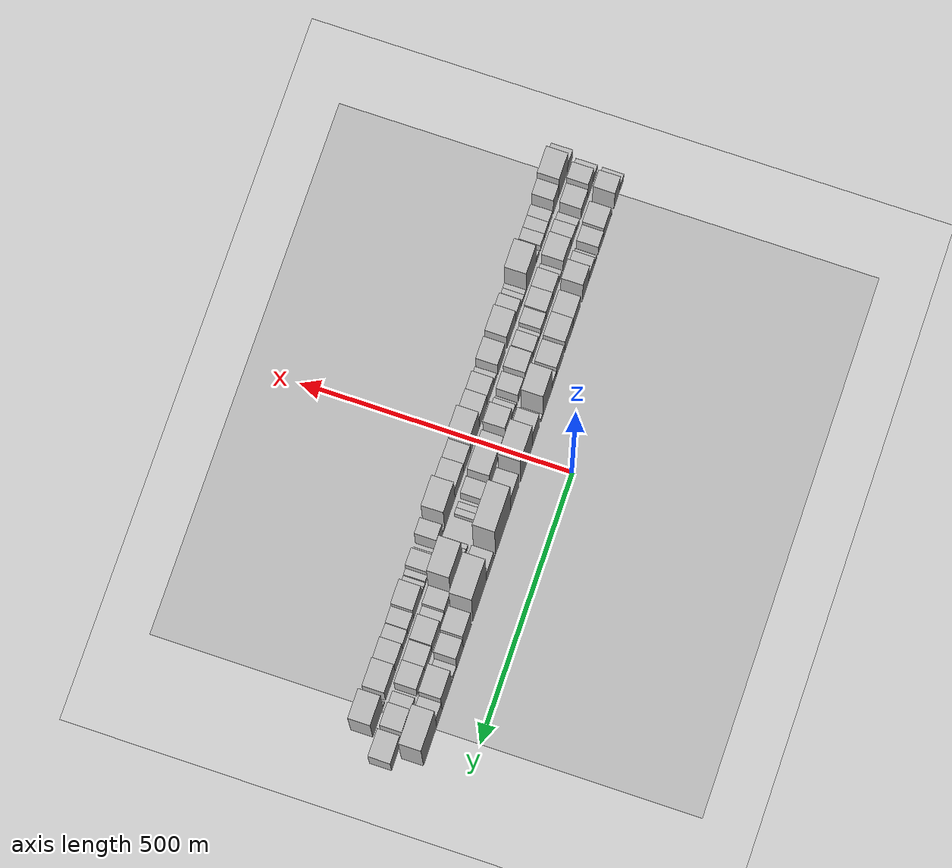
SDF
<?xml version="1.0" encoding="utf-8"?>

<sdf version="1.6">

   <world name="default">

      <gui fullscreen="0">

         <camera name="user_camera">

            <pose>-15 0 4.57585 0 0 0</pose>

            <view_controller>orbit</view_controller>

         </camera>

      </gui>

      <scene>

         <sky>

           <clouds>

             <speed>12</speed>

           </clouds>

         </sky>

         <ambient>0.4 0.4 0.4 1</ambient>

         <background>0.7 0.7 0.7 1</background>

         <shadows>1</shadows>

      </scene>

      <gravity>0 0 -9.8066</gravity>

      <magnetic_field>6e-06 2.3e-05 -4.2e-05</magnetic_field>

      <physics default="0" name="default_physics" type="ode">

         <ode>

            <solver>

               <type>quick</type>

               <iters>10</iters>

               <sor>1.0</sor>

               <use_dynamic_moi_rescaling>0</use_dynamic_moi_rescaling>

            </solver>

            <constraints>

               <cfm>0</cfm>

               <erp>0.2</erp>

               <contact_max_correcting_vel>100</contact_max_correcting_vel>

               <contact_surface_layer>0.001</contact_surface_layer>

            </constraints>

         </ode>

         <max_step_size>0.004</max_step_size>

         <real_time_factor>1</real_time_factor>

         <real_time_update_rate>250</real_time_update_rate>

      </physics>

      <light name="sun" type="directional">

         <cast_shadows>1</cast_shadows>

         <pose>0 0 10 0 0 0</pose>

         <diffuse>0.8 0.8 0.8 1</diffuse>

         <specular>0.2 0.2 0.2 1</specular>

         <attenuation>

            <range>1000</range>

            <constant>0.9</constant>

            <linear>0.01</linear>

            <quadratic>0.001</quadratic>

         </attenuation>

         <direction>-0.5 0.1 -0.9</direction>

      </light>

      <include>

         <name>ground_plane_1</name>

         <uri>model://HANNAS_ground_plane</uri>

         <pose>0 0 0  0 0 0</pose>

      </include>

      <include>

         <name>ground_plane_2</name>

         <uri>model://HANNAS_ground_plane</uri>

         <pose>100 0 0  0 0 0</pose>

      </include>

      <model name="building_1">

         <static>1</static>

         <pose frame="">100.0000 -514.4406 0 0.000000 0.000000 0.000000</pose>

         <link name="link">

            <pose frame="">0 0 21.00 0 0 0</pose>

            <collision name="collision">

               <geometry>

                  <box>

                     <size>40.0000 23.1189 42.0000</size>

                  </box>

               </geometry>

               <max_contacts>10</max_contacts>

               <surface>

                  <contact>

                     <ode/>

                  </contact>

                  <bounce/>

                  <friction>

                     <torsional>

                        <ode/>

                     </torsional>

                     <ode/>

                  </friction>

               </surface>

            </collision>

            <visual name="visual">

               <cast_shadows>0</cast_shadows>

               <geometry>

                  <box>

                     <size>40.0000 23.1189 42.0000</size>

                  </box>

               </geometry>

               <material>

                  <script>

                     <uri>model://HANNAS_wall/materials/scripts</uri>

                     <uri>model://HANNAS_wall/materials/textures</uri>

                     <name>vrc/HANNAS_wall</name>

                  </script>

               </material>

            </visual>

            <self_collide>0</self_collide>

            <enable_wind>0</enable_wind>

            <kinematic>0</kinematic>

         </link>

      </model>

      <model name="building_2">

         <static>1</static>

         <pose frame="">100.0000 -486.9206 0 0.000000 0.000000 0.000000</pose>

         <link name="link">

            <pose frame="">0 0 52.50 0 0 0</pose>

            <collision name="collision">

               <geometry>

                  <box>

                     <size>40.0000 31.9210 105.0000</size>

                  </box>

               </geometry>

               <max_contacts>10</max_contacts>

               <surface>

                  <contact>

                     <ode/>

                  </contact>

                  <bounce/>

                  <friction>

                     <torsional>

                        <ode/>

                     </torsional>

                     <ode/>

                  </friction>

               </surface>

            </collision>

            <visual name="visual">

               <cast_shadows>0</cast_shadows>

               <geometry>

                  <box>

                     <size>40.0000 31.9210 105.0000</size>

                  </box>

               </geometry>

               <material>

                  <script>

                     <uri>model://HANNAS_wall/materials/scripts</uri>

                     <uri>model://HANNAS_wall/materials/textures</uri>

                     <name>vrc/HANNAS_wall</name>

                  </script>

               </material>

            </visual>

            <self_collide>0</self_collide>

            <enable_wind>0</enable_wind>

            <kinematic>0</kinematic>

         </link>

      </model>

      <model name="building_3">

         <static>1</static>

         <pose frame="">100.0000 -457.2206 0 0.000000 0.000000 0.000000</pose>

         <link name="link">

            <pose frame="">0 0 10.50 0 0 0</pose>

            <collision name="collision">

               <geometry>

                  <box>

                     <size>40.0000 9.4788 21.0000</size>

                  </box>

               </geometry>

               <max_contacts>10</max_contacts>

               <surface>

                  <contact>

                     <ode/>

                  </contact>

                  <bounce/>

                  <friction>

                     <torsional>

                        <ode/>

                     </torsional>

                     <ode/>

                  </friction>

               </surface>

            </collision>

            <visual name="visual">

               <cast_shadows>0</cast_shadows>

               <geometry>

                  <box>

                     <size>40.0000 9.4788 21.0000</size>

                  </box>

               </geometry>

               <material>

                  <script>

                     <uri>model://HANNAS_wall/materials/scripts</uri>

                     <uri>model://HANNAS_wall/materials/textures</uri>

                     <name>vrc/HANNAS_wall</name>

                  </script>

               </material>

            </visual>

            <self_collide>0</self_collide>

            <enable_wind>0</enable_wind>

            <kinematic>0</kinematic>

         </link>

      </model>

      <model name="building_4">

         <static>1</static>

         <pose frame="">100.0000 -432.5442 0 0.000000 0.000000 0.000000</pose>

         <link name="link">

            <pose frame="">0 0 37.50 0 0 0</pose>

            <collision name="collision">

               <geometry>

                  <box>

                     <size>40.0000 39.8741 75.0000</size>

                  </box>

               </geometry>

               <max_contacts>10</max_contacts>

               <surface>

                  <contact>

                     <ode/>

                  </contact>

                  <bounce/>

                  <friction>

                     <torsional>

                        <ode/>

                     </torsional>

                     <ode/>

                  </friction>

               </surface>

            </collision>

            <visual name="visual">

               <cast_shadows>0</cast_shadows>

               <geometry>

                  <box>

                     <size>40.0000 39.8741 75.0000</size>

                  </box>

               </geometry>

               <material>

                  <script>

                     <uri>model://HANNAS_wall/materials/scripts</uri>

                     <uri>model://HANNAS_wall/materials/textures</uri>

                     <name>vrc/HANNAS_wall</name>

                  </script>

               </material>

            </visual>

            <self_collide>0</self_collide>

            <enable_wind>0</enable_wind>

            <kinematic>0</kinematic>

         </link>

      </model>

      <model name="building_5">

         <static>1</static>

         <pose frame="">100.0000 -397.4626 0 0.000000 0.000000 0.000000</pose>

         <link name="link">

            <pose frame="">0 0 28.50 0 0 0</pose>

            <collision name="collision">

               <geometry>

                  <box>

                     <size>40.0000 30.2890 57.0000</size>

                  </box>

               </geometry>

               <max_contacts>10</max_contacts>

               <surface>

                  <contact>

                     <ode/>

                  </contact>

                  <bounce/>

                  <friction>

                     <torsional>

                        <ode/>

                     </torsional>

                     <ode/>

                  </friction>

               </surface>

            </collision>

            <visual name="visual">

               <cast_shadows>0</cast_shadows>

               <geometry>

                  <box>

                     <size>40.0000 30.2890 57.0000</size>

                  </box>

               </geometry>

               <material>

                  <script>

                     <uri>model://HANNAS_wall/materials/scripts</uri>

                     <uri>model://HANNAS_wall/materials/textures</uri>

                     <name>vrc/HANNAS_wall</name>

                  </script>

               </material>

            </visual>

            <self_collide>0</self_collide>

            <enable_wind>0</enable_wind>

            <kinematic>0</kinematic>

         </link>

      </model>

      <model name="building_6">

         <static>1</static>

         <pose frame="">100.0000 -369.0856 0 0.000000 0.000000 0.000000</pose>

         <link name="link">

            <pose frame="">0 0 13.50 0 0 0</pose>

            <collision name="collision">

               <geometry>

                  <box>

                     <size>40.0000 12.4650 27.0000</size>

                  </box>

               </geometry>

               <max_contacts>10</max_contacts>

               <surface>

                  <contact>

                     <ode/>

                  </contact>

                  <bounce/>

                  <friction>

                     <torsional>

                        <ode/>

                     </torsional>

                     <ode/>

                  </friction>

               </surface>

            </collision>

            <visual name="visual">

               <cast_shadows>0</cast_shadows>

               <geometry>

                  <box>

                     <size>40.0000 12.4650 27.0000</size>

                  </box>

               </geometry>

               <material>

                  <script>

                     <uri>model://HANNAS_wall/materials/scripts</uri>

                     <uri>model://HANNAS_wall/materials/textures</uri>

                     <name>vrc/HANNAS_wall</name>

                  </script>

               </material>

            </visual>

            <self_collide>0</self_collide>

            <enable_wind>0</enable_wind>

            <kinematic>0</kinematic>

         </link>

      </model>

      <model name="building_7">

         <static>1</static>

         <pose frame="">100.0000 -346.7945 0 0.000000 0.000000 0.000000</pose>

         <link name="link">

            <pose frame="">0 0 30.00 0 0 0</pose>

            <collision name="collision">

               <geometry>

                  <box>

                     <size>40.0000 32.1171 60.0000</size>

                  </box>

               </geometry>

               <max_contacts>10</max_contacts>

               <surface>

                  <contact>

                     <ode/>

                  </contact>

                  <bounce/>

                  <friction>

                     <torsional>

                        <ode/>

                     </torsional>

                     <ode/>

                  </friction>

               </surface>

            </collision>

            <visual name="visual">

               <cast_shadows>0</cast_shadows>

               <geometry>

                  <box>

                     <size>40.0000 32.1171 60.0000</size>

                  </box>

               </geometry>

               <material>

                  <script>

                     <uri>model://HANNAS_wall/materials/scripts</uri>

                     <uri>model://HANNAS_wall/materials/textures</uri>

                     <name>vrc/HANNAS_wall</name>

                  </script>

               </material>

            </visual>

            <self_collide>0</self_collide>

            <enable_wind>0</enable_wind>

            <kinematic>0</kinematic>

         </link>

      </model>

      <model name="building_8">

         <static>1</static>

         <pose frame="">100.0000 -312.5930 0 0.000000 0.000000 0.000000</pose>

         <link name="link">

            <pose frame="">0 0 60.00 0 0 0</pose>

            <collision name="collision">

               <geometry>

                  <box>

                     <size>40.0000 36.2858 120.0000</size>

                  </box>

               </geometry>

               <max_contacts>10</max_contacts>

               <surface>

                  <contact>

                     <ode/>

                  </contact>

                  <bounce/>

                  <friction>

                     <torsional>

                        <ode/>

                     </torsional>

                     <ode/>

                  </friction>

               </surface>

            </collision>

            <visual name="visual">

               <cast_shadows>0</cast_shadows>

               <geometry>

                  <box>

                     <size>40.0000 36.2858 120.0000</size>

                  </box>

               </geometry>

               <material>

                  <script>

                     <uri>model://HANNAS_wall/materials/scripts</uri>

                     <uri>model://HANNAS_wall/materials/textures</uri>

                     <name>vrc/HANNAS_wall</name>

                  </script>

               </material>

            </visual>

            <self_collide>0</self_collide>

            <enable_wind>0</enable_wind>

            <kinematic>0</kinematic>

         </link>

      </model>

      <model name="building_9">

         <static>1</static>

         <pose frame="">100.0000 -263.7543 0 0.000000 0.000000 0.000000</pose>

         <link name="link">

            <pose frame="">0 0 39.00 0 0 0</pose>

            <collision name="collision">

               <geometry>

                  <box>

                     <size>40.0000 41.3915 78.0000</size>

                  </box>

               </geometry>

               <max_contacts>10</max_contacts>

               <surface>

                  <contact>

                     <ode/>

                  </contact>

                  <bounce/>

                  <friction>

                     <torsional>

                        <ode/>

                     </torsional>

                     <ode/>

                  </friction>

               </surface>

            </collision>

            <visual name="visual">

               <cast_shadows>0</cast_shadows>

               <geometry>

                  <box>

                     <size>40.0000 41.3915 78.0000</size>

                  </box>

               </geometry>

               <material>

                  <script>

                     <uri>model://HANNAS_wall/materials/scripts</uri>

                     <uri>model://HANNAS_wall/materials/textures</uri>

                     <name>vrc/HANNAS_wall</name>

                  </script>

               </material>

            </visual>

            <self_collide>0</self_collide>

            <enable_wind>0</enable_wind>

            <kinematic>0</kinematic>

         </link>

      </model>

      <model name="building_10">

         <static>1</static>

         <pose frame="">100.0000 -220.6366 0 0.000000 0.000000 0.000000</pose>

         <link name="link">

            <pose frame="">0 0 40.50 0 0 0</pose>

            <collision name="collision">

               <geometry>

                  <box>

                     <size>40.0000 44.8439 81.0000</size>

                  </box>

               </geometry>

               <max_contacts>10</max_contacts>

               <surface>

                  <contact>

                     <ode/>

                  </contact>

                  <bounce/>

                  <friction>

                     <torsional>

                        <ode/>

                     </torsional>

                     <ode/>

                  </friction>

               </surface>

            </collision>

            <visual name="visual">

               <cast_shadows>0</cast_shadows>

               <geometry>

                  <box>

                     <size>40.0000 44.8439 81.0000</size>

                  </box>

               </geometry>

               <material>

                  <script>

                     <uri>model://HANNAS_wall/materials/scripts</uri>

                     <uri>model://HANNAS_wall/materials/textures</uri>

                     <name>vrc/HANNAS_wall</name>

                  </script>

               </material>

            </visual>

            <self_collide>0</self_collide>

            <enable_wind>0</enable_wind>

            <kinematic>0</kinematic>

         </link>

      </model>

      <model name="building_11">

         <static>1</static>

         <pose frame="">100.0000 -172.2574 0 0.000000 0.000000 0.000000</pose>

         <link name="link">

            <pose frame="">0 0 37.50 0 0 0</pose>

            <collision name="collision">

               <geometry>

                  <box>

                     <size>40.0000 41.9144 75.0000</size>

                  </box>

               </geometry>

               <max_contacts>10</max_contacts>

               <surface>

                  <contact>

                     <ode/>

                  </contact>

                  <bounce/>

                  <friction>

                     <torsional>

                        <ode/>

                     </torsional>

                     <ode/>

                  </friction>

               </surface>

            </collision>

            <visual name="visual">

               <cast_shadows>0</cast_shadows>

               <geometry>

                  <box>

                     <size>40.0000 41.9144 75.0000</size>

                  </box>

               </geometry>

               <material>

                  <script>

                     <uri>model://HANNAS_wall/materials/scripts</uri>

                     <uri>model://HANNAS_wall/materials/textures</uri>

                     <name>vrc/HANNAS_wall</name>

                  </script>

               </material>

            </visual>

            <self_collide>0</self_collide>

            <enable_wind>0</enable_wind>

            <kinematic>0</kinematic>

         </link>

      </model>

      <model name="building_12">

         <static>1</static>

         <pose frame="">100.0000 -139.1292 0 0.000000 0.000000 0.000000</pose>

         <link name="link">

            <pose frame="">0 0 24.00 0 0 0</pose>

            <collision name="collision">

               <geometry>

                  <box>

                     <size>40.0000 24.3419 48.0000</size>

                  </box>

               </geometry>

               <max_contacts>10</max_contacts>

               <surface>

                  <contact>

                     <ode/>

                  </contact>

                  <bounce/>

                  <friction>

                     <torsional>

                        <ode/>

                     </torsional>

                     <ode/>

                  </friction>

               </surface>

            </collision>

            <visual name="visual">

               <cast_shadows>0</cast_shadows>

               <geometry>

                  <box>

                     <size>40.0000 24.3419 48.0000</size>

                  </box>

               </geometry>

               <material>

                  <script>

                     <uri>model://HANNAS_wall/materials/scripts</uri>

                     <uri>model://HANNAS_wall/materials/textures</uri>

                     <name>vrc/HANNAS_wall</name>

                  </script>

               </material>

            </visual>

            <self_collide>0</self_collide>

            <enable_wind>0</enable_wind>

            <kinematic>0</kinematic>

         </link>

      </model>

      <model name="building_13">

         <static>1</static>

         <pose frame="">100.0000 -102.0456 0 0.000000 0.000000 0.000000</pose>

         <link name="link">

            <pose frame="">0 0 82.50 0 0 0</pose>

            <collision name="collision">

               <geometry>

                  <box>

                     <size>40.0000 49.8253 165.0000</size>

                  </box>

               </geometry>

               <max_contacts>10</max_contacts>

               <surface>

                  <contact>

                     <ode/>

                  </contact>

                  <bounce/>

                  <friction>

                     <torsional>

                        <ode/>

                     </torsional>

                     <ode/>

                  </friction>

               </surface>

            </collision>

            <visual name="visual">

               <cast_shadows>0</cast_shadows>

               <geometry>

                  <box>

                     <size>40.0000 49.8253 165.0000</size>

                  </box>

               </geometry>

               <material>

                  <script>

                     <uri>model://HANNAS_wall/materials/scripts</uri>

                     <uri>model://HANNAS_wall/materials/textures</uri>

                     <name>vrc/HANNAS_wall</name>

                  </script>

               </material>

            </visual>

            <self_collide>0</self_collide>

            <enable_wind>0</enable_wind>

            <kinematic>0</kinematic>

         </link>

      </model>

      <model name="building_14">

         <static>1</static>

         <pose frame="">100.0000 -72.2656 0 0.000000 0.000000 0.000000</pose>

         <link name="link">

            <pose frame="">0 0 12.00 0 0 0</pose>

            <collision name="collision">

               <geometry>

                  <box>

                     <size>40.0000 9.7349 24.0000</size>

                  </box>

               </geometry>

               <max_contacts>10</max_contacts>

               <surface>

                  <contact>

                     <ode/>

                  </contact>

                  <bounce/>

                  <friction>

                     <torsional>

                        <ode/>

                     </torsional>

                     <ode/>

                  </friction>

               </surface>

            </collision>

            <visual name="visual">

               <cast_shadows>0</cast_shadows>

               <geometry>

                  <box>

                     <size>40.0000 9.7349 24.0000</size>

                  </box>

               </geometry>

               <material>

                  <script>

                     <uri>model://HANNAS_wall/materials/scripts</uri>

                     <uri>model://HANNAS_wall/materials/textures</uri>

                     <name>vrc/HANNAS_wall</name>

                  </script>

               </material>

            </visual>

            <self_collide>0</self_collide>

            <enable_wind>0</enable_wind>

            <kinematic>0</kinematic>

         </link>

      </model>

      <model name="building_15">

         <static>1</static>

         <pose frame="">100.0000 -38.1251 0 0.000000 0.000000 0.000000</pose>

         <link name="link">

            <pose frame="">0 0 55.50 0 0 0</pose>

            <collision name="collision">

               <geometry>

                  <box>

                     <size>40.0000 38.5460 111.0000</size>

                  </box>

               </geometry>

               <max_contacts>10</max_contacts>

               <surface>

                  <contact>

                     <ode/>

                  </contact>

                  <bounce/>

                  <friction>

                     <torsional>

                        <ode/>

                     </torsional>

                     <ode/>

                  </friction>

               </surface>

            </collision>

            <visual name="visual">

               <cast_shadows>0</cast_shadows>

               <geometry>

                  <box>

                     <size>40.0000 38.5460 111.0000</size>

                  </box>

               </geometry>

               <material>

                  <script>

                     <uri>model://HANNAS_wall/materials/scripts</uri>

                     <uri>model://HANNAS_wall/materials/textures</uri>

                     <name>vrc/HANNAS_wall</name>

                  </script>

               </material>

            </visual>

            <self_collide>0</self_collide>

            <enable_wind>0</enable_wind>

            <kinematic>0</kinematic>

         </link>

      </model>

      <model name="building_16">

         <static>1</static>

         <pose frame="">100.0000 13.4674 0 0.000000 0.000000 0.000000</pose>

         <link name="link">

            <pose frame="">0 0 93.00 0 0 0</pose>

            <collision name="collision">

               <geometry>

                  <box>

                     <size>40.0000 64.6390 186.0000</size>

                  </box>

               </geometry>

               <max_contacts>10</max_contacts>

               <surface>

                  <contact>

                     <ode/>

                  </contact>

                  <bounce/>

                  <friction>

                     <torsional>

                        <ode/>

                     </torsional>

                     <ode/>

                  </friction>

               </surface>

            </collision>

            <visual name="visual">

               <cast_shadows>0</cast_shadows>

               <geometry>

                  <box>

                     <size>40.0000 64.6390 186.0000</size>

                  </box>

               </geometry>

               <material>

                  <script>

                     <uri>model://HANNAS_wall/materials/scripts</uri>

                     <uri>model://HANNAS_wall/materials/textures</uri>

                     <name>vrc/HANNAS_wall</name>

                  </script>

               </material>

            </visual>

            <self_collide>0</self_collide>

            <enable_wind>0</enable_wind>

            <kinematic>0</kinematic>

         </link>

      </model>

      <model name="building_17">

         <static>1</static>

         <pose frame="">100.0000 77.0837 0 0.000000 0.000000 0.000000</pose>

         <link name="link">

            <pose frame="">0 0 58.50 0 0 0</pose>

            <collision name="collision">

               <geometry>

                  <box>

                     <size>40.0000 44.5935 117.0000</size>

                  </box>

               </geometry>

               <max_contacts>10</max_contacts>

               <surface>

                  <contact>

                     <ode/>

                  </contact>

                  <bounce/>

                  <friction>

                     <torsional>

                        <ode/>

                     </torsional>

                     <ode/>

                  </friction>

               </surface>

            </collision>

            <visual name="visual">

               <cast_shadows>0</cast_shadows>

               <geometry>

                  <box>

                     <size>40.0000 44.5935 117.0000</size>

                  </box>

               </geometry>

               <material>

                  <script>

                     <uri>model://HANNAS_wall/materials/scripts</uri>

                     <uri>model://HANNAS_wall/materials/textures</uri>

                     <name>vrc/HANNAS_wall</name>

                  </script>

               </material>

            </visual>

            <self_collide>0</self_collide>

            <enable_wind>0</enable_wind>

            <kinematic>0</kinematic>

         </link>

      </model>

      <model name="building_18">

         <static>1</static>

         <pose frame="">100.0000 140.0702 0 0.000000 0.000000 0.000000</pose>

         <link name="link">

            <pose frame="">0 0 111.00 0 0 0</pose>

            <collision name="collision">

               <geometry>

                  <box>

                     <size>40.0000 81.3795 222.0000</size>

                  </box>

               </geometry>

               <max_contacts>10</max_contacts>

               <surface>

                  <contact>

                     <ode/>

                  </contact>

                  <bounce/>

                  <friction>

                     <torsional>

                        <ode/>

                     </torsional>

                     <ode/>

                  </friction>

               </surface>

            </collision>

            <visual name="visual">

               <cast_shadows>0</cast_shadows>

               <geometry>

                  <box>

                     <size>40.0000 81.3795 222.0000</size>

                  </box>

               </geometry>

               <material>

                  <script>

                     <uri>model://HANNAS_wall/materials/scripts</uri>

                     <uri>model://HANNAS_wall/materials/textures</uri>

                     <name>vrc/HANNAS_wall</name>

                  </script>

               </material>

            </visual>

            <self_collide>0</self_collide>

            <enable_wind>0</enable_wind>

            <kinematic>0</kinematic>

         </link>

      </model>

      <model name="building_19">

         <static>1</static>

         <pose frame="">100.0000 184.8015 0 0.000000 0.000000 0.000000</pose>

         <link name="link">

            <pose frame="">0 0 9.00 0 0 0</pose>

            <collision name="collision">

               <geometry>

                  <box>

                     <size>40.0000 8.0831 18.0000</size>

                  </box>

               </geometry>

               <max_contacts>10</max_contacts>

               <surface>

                  <contact>

                     <ode/>

                  </contact>

                  <bounce/>

                  <friction>

                     <torsional>

                        <ode/>

                     </torsional>

                     <ode/>

                  </friction>

               </surface>

            </collision>

            <visual name="visual">

               <cast_shadows>0</cast_shadows>

               <geometry>

                  <box>

                     <size>40.0000 8.0831 18.0000</size>

                  </box>

               </geometry>

               <material>

                  <script>

                     <uri>model://HANNAS_wall/materials/scripts</uri>

                     <uri>model://HANNAS_wall/materials/textures</uri>

                     <name>vrc/HANNAS_wall</name>

                  </script>

               </material>

            </visual>

            <self_collide>0</self_collide>

            <enable_wind>0</enable_wind>

            <kinematic>0</kinematic>

         </link>

      </model>

      <model name="building_20">

         <static>1</static>

         <pose frame="">100.0000 209.0936 0 0.000000 0.000000 0.000000</pose>

         <link name="link">

            <pose frame="">0 0 37.50 0 0 0</pose>

            <collision name="collision">

               <geometry>

                  <box>

                     <size>40.0000 40.5012 75.0000</size>

                  </box>

               </geometry>

               <max_contacts>10</max_contacts>

               <surface>

                  <contact>

                     <ode/>

                  </contact>

                  <bounce/>

                  <friction>

                     <torsional>

                        <ode/>

                     </torsional>

                     <ode/>

                  </friction>

               </surface>

            </collision>

            <visual name="visual">

               <cast_shadows>0</cast_shadows>

               <geometry>

                  <box>

                     <size>40.0000 40.5012 75.0000</size>

                  </box>

               </geometry>

               <material>

                  <script>

                     <uri>model://HANNAS_wall/materials/scripts</uri>

                     <uri>model://HANNAS_wall/materials/textures</uri>

                     <name>vrc/HANNAS_wall</name>

                  </script>

               </material>

            </visual>

            <self_collide>0</self_collide>

            <enable_wind>0</enable_wind>

            <kinematic>0</kinematic>

         </link>

      </model>

      <model name="building_21">

         <static>1</static>

         <pose frame="">100.0000 266.0082 0 0.000000 0.000000 0.000000</pose>

         <link name="link">

            <pose frame="">0 0 111.00 0 0 0</pose>

            <collision name="collision">

               <geometry>

                  <box>

                     <size>40.0000 73.3279 222.0000</size>

                  </box>

               </geometry>

               <max_contacts>10</max_contacts>

               <surface>

                  <contact>

                     <ode/>

                  </contact>

                  <bounce/>

                  <friction>

                     <torsional>

                        <ode/>

                     </torsional>

                     <ode/>

                  </friction>

               </surface>

            </collision>

            <visual name="visual">

               <cast_shadows>0</cast_shadows>

               <geometry>

                  <box>

                     <size>40.0000 73.3279 222.0000</size>

                  </box>

               </geometry>

               <material>

                  <script>

                     <uri>model://HANNAS_wall/materials/scripts</uri>

                     <uri>model://HANNAS_wall/materials/textures</uri>

                     <name>vrc/HANNAS_wall</name>

                  </script>

               </material>

            </visual>

            <self_collide>0</self_collide>

            <enable_wind>0</enable_wind>

            <kinematic>0</kinematic>

         </link>

      </model>

      <model name="building_22">

         <static>1</static>

         <pose frame="">100.0000 331.4703 0 0.000000 0.000000 0.000000</pose>

         <link name="link">

            <pose frame="">0 0 66.00 0 0 0</pose>

            <collision name="collision">

               <geometry>

                  <box>

                     <size>40.0000 43.5963 132.0000</size>

                  </box>

               </geometry>

               <max_contacts>10</max_contacts>

               <surface>

                  <contact>

                     <ode/>

                  </contact>

                  <bounce/>

                  <friction>

                     <torsional>

                        <ode/>

                     </torsional>

                     <ode/>

                  </friction>

               </surface>

            </collision>

            <visual name="visual">

               <cast_shadows>0</cast_shadows>

               <geometry>

                  <box>

                     <size>40.0000 43.5963 132.0000</size>

                  </box>

               </geometry>

               <material>

                  <script>

                     <uri>model://HANNAS_wall/materials/scripts</uri>

                     <uri>model://HANNAS_wall/materials/textures</uri>

                     <name>vrc/HANNAS_wall</name>

                  </script>

               </material>

            </visual>

            <self_collide>0</self_collide>

            <enable_wind>0</enable_wind>

            <kinematic>0</kinematic>

         </link>

      </model>

      <model name="building_23">

         <static>1</static>

         <pose frame="">100.0000 371.3016 0 0.000000 0.000000 0.000000</pose>

         <link name="link">

            <pose frame="">0 0 54.00 0 0 0</pose>

            <collision name="collision">

               <geometry>

                  <box>

                     <size>40.0000 36.0664 108.0000</size>

                  </box>

               </geometry>

               <max_contacts>10</max_contacts>

               <surface>

                  <contact>

                     <ode/>

                  </contact>

                  <bounce/>

                  <friction>

                     <torsional>

                        <ode/>

                     </torsional>

                     <ode/>

                  </friction>

               </surface>

            </collision>

            <visual name="visual">

               <cast_shadows>0</cast_shadows>

               <geometry>

                  <box>

                     <size>40.0000 36.0664 108.0000</size>

                  </box>

               </geometry>

               <material>

                  <script>

                     <uri>model://HANNAS_wall/materials/scripts</uri>

                     <uri>model://HANNAS_wall/materials/textures</uri>

                     <name>vrc/HANNAS_wall</name>

                  </script>

               </material>

            </visual>

            <self_collide>0</self_collide>

            <enable_wind>0</enable_wind>

            <kinematic>0</kinematic>

         </link>

      </model>

      <model name="building_24">

         <static>1</static>

         <pose frame="">100.0000 399.0295 0 0.000000 0.000000 0.000000</pose>

         <link name="link">

            <pose frame="">0 0 16.50 0 0 0</pose>

            <collision name="collision">

               <geometry>

                  <box>

                     <size>40.0000 19.3893 33.0000</size>

                  </box>

               </geometry>

               <max_contacts>10</max_contacts>

               <surface>

                  <contact>

                     <ode/>

                  </contact>

                  <bounce/>

                  <friction>

                     <torsional>

                        <ode/>

                     </torsional>

                     <ode/>

                  </friction>

               </surface>

            </collision>

            <visual name="visual">

               <cast_shadows>0</cast_shadows>

               <geometry>

                  <box>

                     <size>40.0000 19.3893 33.0000</size>

                  </box>

               </geometry>

               <material>

                  <script>

                     <uri>model://HANNAS_wall/materials/scripts</uri>

                     <uri>model://HANNAS_wall/materials/textures</uri>

                     <name>vrc/HANNAS_wall</name>

                  </script>

               </material>

            </visual>

            <self_collide>0</self_collide>

            <enable_wind>0</enable_wind>

            <kinematic>0</kinematic>

         </link>

      </model>

      <model name="building_25">

         <static>1</static>

         <pose frame="">100.0000 412.3815 0 0.000000 0.000000 0.000000</pose>

         <link name="link">

            <pose frame="">0 0 7.50 0 0 0</pose>

            <collision name="collision">

               <geometry>

                  <box>

                     <size>40.0000 7.3146 15.0000</size>

                  </box>

               </geometry>

               <max_contacts>10</max_contacts>

               <surface>

                  <contact>

                     <ode/>

                  </contact>

                  <bounce/>

                  <friction>

                     <torsional>

                        <ode/>

                     </torsional>

                     <ode/>

                  </friction>

               </surface>

            </collision>

            <visual name="visual">

               <cast_shadows>0</cast_shadows>

               <geometry>

                  <box>

                     <size>40.0000 7.3146 15.0000</size>

                  </box>

               </geometry>

               <material>

                  <script>

                     <uri>model://HANNAS_wall/materials/scripts</uri>

                     <uri>model://HANNAS_wall/materials/textures</uri>

                     <name>vrc/HANNAS_wall</name>

                  </script>

               </material>

            </visual>

            <self_collide>0</self_collide>

            <enable_wind>0</enable_wind>

            <kinematic>0</kinematic>

         </link>

      </model>

      <model name="building_26">

         <static>1</static>

         <pose frame="">100.0000 441.1914 0 0.000000 0.000000 0.000000</pose>

         <link name="link">

            <pose frame="">0 0 72.00 0 0 0</pose>

            <collision name="collision">

               <geometry>

                  <box>

                     <size>40.0000 50.3052 144.0000</size>

                  </box>

               </geometry>

               <max_contacts>10</max_contacts>

               <surface>

                  <contact>

                     <ode/>

                  </contact>

                  <bounce/>

                  <friction>

                     <torsional>

                        <ode/>

                     </torsional>

                     <ode/>

                  </friction>

               </surface>

            </collision>

            <visual name="visual">

               <cast_shadows>0</cast_shadows>

               <geometry>

                  <box>

                     <size>40.0000 50.3052 144.0000</size>

                  </box>

               </geometry>

               <material>

                  <script>

                     <uri>model://HANNAS_wall/materials/scripts</uri>

                     <uri>model://HANNAS_wall/materials/textures</uri>

                     <name>vrc/HANNAS_wall</name>

                  </script>

               </material>

            </visual>

            <self_collide>0</self_collide>

            <enable_wind>0</enable_wind>

            <kinematic>0</kinematic>

         </link>

      </model>

      <model name="building_27">

         <static>1</static>

         <pose frame="">100.0000 481.0401 0 0.000000 0.000000 0.000000</pose>

         <link name="link">

            <pose frame="">0 0 48.00 0 0 0</pose>

            <collision name="collision">

               <geometry>

                  <box>

                     <size>40.0000 29.3922 96.0000</size>

                  </box>

               </geometry>

               <max_contacts>10</max_contacts>

               <surface>

                  <contact>

                     <ode/>

                  </contact>

                  <bounce/>

                  <friction>

                     <torsional>

                        <ode/>

                     </torsional>

                     <ode/>

                  </friction>

               </surface>

            </collision>

            <visual name="visual">

               <cast_shadows>0</cast_shadows>

               <geometry>

                  <box>

                     <size>40.0000 29.3922 96.0000</size>

                  </box>

               </geometry>

               <material>

                  <script>

                     <uri>model://HANNAS_wall/materials/scripts</uri>

                     <uri>model://HANNAS_wall/materials/textures</uri>

                     <name>vrc/HANNAS_wall</name>

                  </script>

               </material>

            </visual>

            <self_collide>0</self_collide>

            <enable_wind>0</enable_wind>

            <kinematic>0</kinematic>

         </link>

      </model>

      <model name="building_28">

         <static>1</static>

         <pose frame="">100.0000 530.9056 0 0.000000 0.000000 0.000000</pose>

         <link name="link">

            <pose frame="">0 0 96.00 0 0 0</pose>

            <collision name="collision">

               <geometry>

                  <box>

                     <size>40.0000 70.3389 192.0000</size>

                  </box>

               </geometry>

               <max_contacts>10</max_contacts>

               <surface>

                  <contact>

                     <ode/>

                  </contact>

                  <bounce/>

                  <friction>

                     <torsional>

                        <ode/>

                     </torsional>

                     <ode/>

                  </friction>

               </surface>

            </collision>

            <visual name="visual">

               <cast_shadows>0</cast_shadows>

               <geometry>

                  <box>

                     <size>40.0000 70.3389 192.0000</size>

                  </box>

               </geometry>

               <material>

                  <script>

                     <uri>model://HANNAS_wall/materials/scripts</uri>

                     <uri>model://HANNAS_wall/materials/textures</uri>

                     <name>vrc/HANNAS_wall</name>

                  </script>

               </material>

            </visual>

            <self_collide>0</self_collide>

            <enable_wind>0</enable_wind>

            <kinematic>0</kinematic>

         </link>

      </model>

      <model name="building_29">

         <static>1</static>

         <pose frame="">149.0000 -514.3529 0 0.000000 0.000000 0.000000</pose>

         <link name="link">

            <pose frame="">0 0 22.50 0 0 0</pose>

            <collision name="collision">

               <geometry>

                  <box>

                     <size>40.0000 23.2941 45.0000</size>

                  </box>

               </geometry>

               <max_contacts>10</max_contacts>

               <surface>

                  <contact>

                     <ode/>

                  </contact>

                  <bounce/>

                  <friction>

                     <torsional>

                        <ode/>

                     </torsional>

                     <ode/>

                  </friction>

               </surface>

            </collision>

            <visual name="visual">

               <cast_shadows>0</cast_shadows>

               <geometry>

                  <box>

                     <size>40.0000 23.2941 45.0000</size>

                  </box>

               </geometry>

               <material>

                  <script>

                     <uri>model://HANNAS_wall/materials/scripts</uri>

                     <uri>model://HANNAS_wall/materials/textures</uri>

                     <name>vrc/HANNAS_wall</name>

                  </script>

               </material>

            </visual>

            <self_collide>0</self_collide>

            <enable_wind>0</enable_wind>

            <kinematic>0</kinematic>

         </link>

      </model>

      <model name="building_30">

         <static>1</static>

         <pose frame="">149.0000 -487.4000 0 0.000000 0.000000 0.000000</pose>

         <link name="link">

            <pose frame="">0 0 51.00 0 0 0</pose>

            <collision name="collision">

               <geometry>

                  <box>

                     <size>40.0000 30.6118 102.0000</size>

                  </box>

               </geometry>

               <max_contacts>10</max_contacts>

               <surface>

                  <contact>

                     <ode/>

                  </contact>

                  <bounce/>

                  <friction>

                     <torsional>

                        <ode/>

                     </torsional>

                     <ode/>

                  </friction>

               </surface>

            </collision>

            <visual name="visual">

               <cast_shadows>0</cast_shadows>

               <geometry>

                  <box>

                     <size>40.0000 30.6118 102.0000</size>

                  </box>

               </geometry>

               <material>

                  <script>

                     <uri>model://HANNAS_wall/materials/scripts</uri>

                     <uri>model://HANNAS_wall/materials/textures</uri>

                     <name>vrc/HANNAS_wall</name>

                  </script>

               </material>

            </visual>

            <self_collide>0</self_collide>

            <enable_wind>0</enable_wind>

            <kinematic>0</kinematic>

         </link>

      </model>

      <model name="building_31">

         <static>1</static>

         <pose frame="">149.0000 -453.6381 0 0.000000 0.000000 0.000000</pose>

         <link name="link">

            <pose frame="">0 0 34.50 0 0 0</pose>

            <collision name="collision">

               <geometry>

                  <box>

                     <size>40.0000 36.9121 69.0000</size>

                  </box>

               </geometry>

               <max_contacts>10</max_contacts>

               <surface>

                  <contact>

                     <ode/>

                  </contact>

                  <bounce/>

                  <friction>

                     <torsional>

                        <ode/>

                     </torsional>

                     <ode/>

                  </friction>

               </surface>

            </collision>

            <visual name="visual">

               <cast_shadows>0</cast_shadows>

               <geometry>

                  <box>

                     <size>40.0000 36.9121 69.0000</size>

                  </box>

               </geometry>

               <material>

                  <script>

                     <uri>model://HANNAS_wall/materials/scripts</uri>

                     <uri>model://HANNAS_wall/materials/textures</uri>

                     <name>vrc/HANNAS_wall</name>

                  </script>

               </material>

            </visual>

            <self_collide>0</self_collide>

            <enable_wind>0</enable_wind>

            <kinematic>0</kinematic>

         </link>

      </model>

      <model name="building_32">

         <static>1</static>

         <pose frame="">149.0000 -417.5335 0 0.000000 0.000000 0.000000</pose>

         <link name="link">

            <pose frame="">0 0 16.50 0 0 0</pose>

            <collision name="collision">

               <geometry>

                  <box>

                     <size>40.0000 19.2970 33.0000</size>

                  </box>

               </geometry>

               <max_contacts>10</max_contacts>

               <surface>

                  <contact>

                     <ode/>

                  </contact>

                  <bounce/>

                  <friction>

                     <torsional>

                        <ode/>

                     </torsional>

                     <ode/>

                  </friction>

               </surface>

            </collision>

            <visual name="visual">

               <cast_shadows>0</cast_shadows>

               <geometry>

                  <box>

                     <size>40.0000 19.2970 33.0000</size>

                  </box>

               </geometry>

               <material>

                  <script>

                     <uri>model://HANNAS_wall/materials/scripts</uri>

                     <uri>model://HANNAS_wall/materials/textures</uri>

                     <name>vrc/HANNAS_wall</name>

                  </script>

               </material>

            </visual>

            <self_collide>0</self_collide>

            <enable_wind>0</enable_wind>

            <kinematic>0</kinematic>

         </link>

      </model>

      <model name="building_33">

         <static>1</static>

         <pose frame="">149.0000 -393.2824 0 0.000000 0.000000 0.000000</pose>

         <link name="link">

            <pose frame="">0 0 27.00 0 0 0</pose>

            <collision name="collision">

               <geometry>

                  <box>

                     <size>40.0000 29.2052 54.0000</size>

                  </box>

               </geometry>

               <max_contacts>10</max_contacts>

               <surface>

                  <contact>

                     <ode/>

                  </contact>

                  <bounce/>

                  <friction>

                     <torsional>

                        <ode/>

                     </torsional>

                     <ode/>

                  </friction>

               </surface>

            </collision>

            <visual name="visual">

               <cast_shadows>0</cast_shadows>

               <geometry>

                  <box>

                     <size>40.0000 29.2052 54.0000</size>

                  </box>

               </geometry>

               <material>

                  <script>

                     <uri>model://HANNAS_wall/materials/scripts</uri>

                     <uri>model://HANNAS_wall/materials/textures</uri>

                     <name>vrc/HANNAS_wall</name>

                  </script>

               </material>

            </visual>

            <self_collide>0</self_collide>

            <enable_wind>0</enable_wind>

            <kinematic>0</kinematic>

         </link>

      </model>

      <model name="building_34">

         <static>1</static>

         <pose frame="">149.0000 -356.8397 0 0.000000 0.000000 0.000000</pose>

         <link name="link">

            <pose frame="">0 0 37.50 0 0 0</pose>

            <collision name="collision">

               <geometry>

                  <box>

                     <size>40.0000 43.6803 75.0000</size>

                  </box>

               </geometry>

               <max_contacts>10</max_contacts>

               <surface>

                  <contact>

                     <ode/>

                  </contact>

                  <bounce/>

                  <friction>

                     <torsional>

                        <ode/>

                     </torsional>

                     <ode/>

                  </friction>

               </surface>

            </collision>

            <visual name="visual">

               <cast_shadows>0</cast_shadows>

               <geometry>

                  <box>

                     <size>40.0000 43.6803 75.0000</size>

                  </box>

               </geometry>

               <material>

                  <script>

                     <uri>model://HANNAS_wall/materials/scripts</uri>

                     <uri>model://HANNAS_wall/materials/textures</uri>

                     <name>vrc/HANNAS_wall</name>

                  </script>

               </material>

            </visual>

            <self_collide>0</self_collide>

            <enable_wind>0</enable_wind>

            <kinematic>0</kinematic>

         </link>

      </model>

      <model name="building_35">

         <static>1</static>

         <pose frame="">149.0000 -321.6928 0 0.000000 0.000000 0.000000</pose>

         <link name="link">

            <pose frame="">0 0 15.00 0 0 0</pose>

            <collision name="collision">

               <geometry>

                  <box>

                     <size>40.0000 16.6135 30.0000</size>

                  </box>

               </geometry>

               <max_contacts>10</max_contacts>

               <surface>

                  <contact>

                     <ode/>

                  </contact>

                  <bounce/>

                  <friction>

                     <torsional>

                        <ode/>

                     </torsional>

                     <ode/>

                  </friction>

               </surface>

            </collision>

            <visual name="visual">

               <cast_shadows>0</cast_shadows>

               <geometry>

                  <box>

                     <size>40.0000 16.6135 30.0000</size>

                  </box>

               </geometry>

               <material>

                  <script>

                     <uri>model://HANNAS_wall/materials/scripts</uri>

                     <uri>model://HANNAS_wall/materials/textures</uri>

                     <name>vrc/HANNAS_wall</name>

                  </script>

               </material>

            </visual>

            <self_collide>0</self_collide>

            <enable_wind>0</enable_wind>

            <kinematic>0</kinematic>

         </link>

      </model>

      <model name="building_36">

         <static>1</static>

         <pose frame="">149.0000 -295.9708 0 0.000000 0.000000 0.000000</pose>

         <link name="link">

            <pose frame="">0 0 33.00 0 0 0</pose>

            <collision name="collision">

               <geometry>

                  <box>

                     <size>40.0000 34.8304 66.0000</size>

                  </box>

               </geometry>

               <max_contacts>10</max_contacts>

               <surface>

                  <contact>

                     <ode/>

                  </contact>

                  <bounce/>

                  <friction>

                     <torsional>

                        <ode/>

                     </torsional>

                     <ode/>

                  </friction>

               </surface>

            </collision>

            <visual name="visual">

               <cast_shadows>0</cast_shadows>

               <geometry>

                  <box>

                     <size>40.0000 34.8304 66.0000</size>

                  </box>

               </geometry>

               <material>

                  <script>

                     <uri>model://HANNAS_wall/materials/scripts</uri>

                     <uri>model://HANNAS_wall/materials/textures</uri>

                     <name>vrc/HANNAS_wall</name>

                  </script>

               </material>

            </visual>

            <self_collide>0</self_collide>

            <enable_wind>0</enable_wind>

            <kinematic>0</kinematic>

         </link>

      </model>

      <model name="building_37">

         <static>1</static>

         <pose frame="">149.0000 -260.1752 0 0.000000 0.000000 0.000000</pose>

         <link name="link">

            <pose frame="">0 0 33.00 0 0 0</pose>

            <collision name="collision">

               <geometry>

                  <box>

                     <size>40.0000 36.7608 66.0000</size>

                  </box>

               </geometry>

               <max_contacts>10</max_contacts>

               <surface>

                  <contact>

                     <ode/>

                  </contact>

                  <bounce/>

                  <friction>

                     <torsional>

                        <ode/>

                     </torsional>

                     <ode/>

                  </friction>

               </surface>

            </collision>

            <visual name="visual">

               <cast_shadows>0</cast_shadows>

               <geometry>

                  <box>

                     <size>40.0000 36.7608 66.0000</size>

                  </box>

               </geometry>

               <material>

                  <script>

                     <uri>model://HANNAS_wall/materials/scripts</uri>

                     <uri>model://HANNAS_wall/materials/textures</uri>

                     <name>vrc/HANNAS_wall</name>

                  </script>

               </material>

            </visual>

            <self_collide>0</self_collide>

            <enable_wind>0</enable_wind>

            <kinematic>0</kinematic>

         </link>

      </model>

      <model name="building_38">

         <static>1</static>

         <pose frame="">149.0000 -226.7297 0 0.000000 0.000000 0.000000</pose>

         <link name="link">

            <pose frame="">0 0 28.50 0 0 0</pose>

            <collision name="collision">

               <geometry>

                  <box>

                     <size>40.0000 30.1301 57.0000</size>

                  </box>

               </geometry>

               <max_contacts>10</max_contacts>

               <surface>

                  <contact>

                     <ode/>

                  </contact>

                  <bounce/>

                  <friction>

                     <torsional>

                        <ode/>

                     </torsional>

                     <ode/>

                  </friction>

               </surface>

            </collision>

            <visual name="visual">

               <cast_shadows>0</cast_shadows>

               <geometry>

                  <box>

                     <size>40.0000 30.1301 57.0000</size>

                  </box>

               </geometry>

               <material>

                  <script>

                     <uri>model://HANNAS_wall/materials/scripts</uri>

                     <uri>model://HANNAS_wall/materials/textures</uri>

                     <name>vrc/HANNAS_wall</name>

                  </script>

               </material>

            </visual>

            <self_collide>0</self_collide>

            <enable_wind>0</enable_wind>

            <kinematic>0</kinematic>

         </link>

      </model>

      <model name="building_39">

         <static>1</static>

         <pose frame="">149.0000 -205.6202 0 0.000000 0.000000 0.000000</pose>

         <link name="link">

            <pose frame="">0 0 13.50 0 0 0</pose>

            <collision name="collision">

               <geometry>

                  <box>

                     <size>40.0000 12.0890 27.0000</size>

                  </box>

               </geometry>

               <max_contacts>10</max_contacts>

               <surface>

                  <contact>

                     <ode/>

                  </contact>

                  <bounce/>

                  <friction>

                     <torsional>

                        <ode/>

                     </torsional>

                     <ode/>

                  </friction>

               </surface>

            </collision>

            <visual name="visual">

               <cast_shadows>0</cast_shadows>

               <geometry>

                  <box>

                     <size>40.0000 12.0890 27.0000</size>

                  </box>

               </geometry>

               <material>

                  <script>

                     <uri>model://HANNAS_wall/materials/scripts</uri>

                     <uri>model://HANNAS_wall/materials/textures</uri>

                     <name>vrc/HANNAS_wall</name>

                  </script>

               </material>

            </visual>

            <self_collide>0</self_collide>

            <enable_wind>0</enable_wind>

            <kinematic>0</kinematic>

         </link>

      </model>

      <model name="building_40">

         <static>1</static>

         <pose frame="">149.0000 -184.9262 0 0.000000 0.000000 0.000000</pose>

         <link name="link">

            <pose frame="">0 0 25.50 0 0 0</pose>

            <collision name="collision">

               <geometry>

                  <box>

                     <size>40.0000 29.2991 51.0000</size>

                  </box>

               </geometry>

               <max_contacts>10</max_contacts>

               <surface>

                  <contact>

                     <ode/>

                  </contact>

                  <bounce/>

                  <friction>

                     <torsional>

                        <ode/>

                     </torsional>

                     <ode/>

                  </friction>

               </surface>

            </collision>

            <visual name="visual">

               <cast_shadows>0</cast_shadows>

               <geometry>

                  <box>

                     <size>40.0000 29.2991 51.0000</size>

                  </box>

               </geometry>

               <material>

                  <script>

                     <uri>model://HANNAS_wall/materials/scripts</uri>

                     <uri>model://HANNAS_wall/materials/textures</uri>

                     <name>vrc/HANNAS_wall</name>

                  </script>

               </material>

            </visual>

            <self_collide>0</self_collide>

            <enable_wind>0</enable_wind>

            <kinematic>0</kinematic>

         </link>

      </model>

      <model name="building_41">

         <static>1</static>

         <pose frame="">149.0000 -146.1866 0 0.000000 0.000000 0.000000</pose>

         <link name="link">

            <pose frame="">0 0 34.50 0 0 0</pose>

            <collision name="collision">

               <geometry>

                  <box>

                     <size>40.0000 38.1800 69.0000</size>

                  </box>

               </geometry>

               <max_contacts>10</max_contacts>

               <surface>

                  <contact>

                     <ode/>

                  </contact>

                  <bounce/>

                  <friction>

                     <torsional>

                        <ode/>

                     </torsional>

                     <ode/>

                  </friction>

               </surface>

            </collision>

            <visual name="visual">

               <cast_shadows>0</cast_shadows>

               <geometry>

                  <box>

                     <size>40.0000 38.1800 69.0000</size>

                  </box>

               </geometry>

               <material>

                  <script>

                     <uri>model://HANNAS_wall/materials/scripts</uri>

                     <uri>model://HANNAS_wall/materials/textures</uri>

                     <name>vrc/HANNAS_wall</name>

                  </script>

               </material>

            </visual>

            <self_collide>0</self_collide>

            <enable_wind>0</enable_wind>

            <kinematic>0</kinematic>

         </link>

      </model>

      <model name="building_42">

         <static>1</static>

         <pose frame="">149.0000 -103.7100 0 0.000000 0.000000 0.000000</pose>

         <link name="link">

            <pose frame="">0 0 30.00 0 0 0</pose>

            <collision name="collision">

               <geometry>

                  <box>

                     <size>40.0000 32.7732 60.0000</size>

                  </box>

               </geometry>

               <max_contacts>10</max_contacts>

               <surface>

                  <contact>

                     <ode/>

                  </contact>

                  <bounce/>

                  <friction>

                     <torsional>

                        <ode/>

                     </torsional>

                     <ode/>

                  </friction>

               </surface>

            </collision>

            <visual name="visual">

               <cast_shadows>0</cast_shadows>

               <geometry>

                  <box>

                     <size>40.0000 32.7732 60.0000</size>

                  </box>

               </geometry>

               <material>

                  <script>

                     <uri>model://HANNAS_wall/materials/scripts</uri>

                     <uri>model://HANNAS_wall/materials/textures</uri>

                     <name>vrc/HANNAS_wall</name>

                  </script>

               </material>

            </visual>

            <self_collide>0</self_collide>

            <enable_wind>0</enable_wind>

            <kinematic>0</kinematic>

         </link>

      </model>

      <model name="building_43">

         <static>1</static>

         <pose frame="">149.0000 -79.4337 0 0.000000 0.000000 0.000000</pose>

         <link name="link">

            <pose frame="">0 0 9.00 0 0 0</pose>

            <collision name="collision">

               <geometry>

                  <box>

                     <size>40.0000 7.7794 18.0000</size>

                  </box>

               </geometry>

               <max_contacts>10</max_contacts>

               <surface>

                  <contact>

                     <ode/>

                  </contact>

                  <bounce/>

                  <friction>

                     <torsional>

                        <ode/>

                     </torsional>

                     <ode/>

                  </friction>

               </surface>

            </collision>

            <visual name="visual">

               <cast_shadows>0</cast_shadows>

               <geometry>

                  <box>

                     <size>40.0000 7.7794 18.0000</size>

                  </box>

               </geometry>

               <material>

                  <script>

                     <uri>model://HANNAS_wall/materials/scripts</uri>

                     <uri>model://HANNAS_wall/materials/textures</uri>

                     <name>vrc/HANNAS_wall</name>

                  </script>

               </material>

            </visual>

            <self_collide>0</self_collide>

            <enable_wind>0</enable_wind>

            <kinematic>0</kinematic>

         </link>

      </model>

      <model name="building_44">

         <static>1</static>

         <pose frame="">149.0000 -64.6756 0 0.000000 0.000000 0.000000</pose>

         <link name="link">

            <pose frame="">0 0 19.50 0 0 0</pose>

            <collision name="collision">

               <geometry>

                  <box>

                     <size>40.0000 21.7368 39.0000</size>

                  </box>

               </geometry>

               <max_contacts>10</max_contacts>

               <surface>

                  <contact>

                     <ode/>

                  </contact>

                  <bounce/>

                  <friction>

                     <torsional>

                        <ode/>

                     </torsional>

                     <ode/>

                  </friction>

               </surface>

            </collision>

            <visual name="visual">

               <cast_shadows>0</cast_shadows>

               <geometry>

                  <box>

                     <size>40.0000 21.7368 39.0000</size>

                  </box>

               </geometry>

               <material>

                  <script>

                     <uri>model://HANNAS_wall/materials/scripts</uri>

                     <uri>model://HANNAS_wall/materials/textures</uri>

                     <name>vrc/HANNAS_wall</name>

                  </script>

               </material>

            </visual>

            <self_collide>0</self_collide>

            <enable_wind>0</enable_wind>

            <kinematic>0</kinematic>

         </link>

      </model>

      <model name="building_45">

         <static>1</static>

         <pose frame="">149.0000 -35.3966 0 0.000000 0.000000 0.000000</pose>

         <link name="link">

            <pose frame="">0 0 49.50 0 0 0</pose>

            <collision name="collision">

               <geometry>

                  <box>

                     <size>40.0000 36.8211 99.0000</size>

                  </box>

               </geometry>

               <max_contacts>10</max_contacts>

               <surface>

                  <contact>

                     <ode/>

                  </contact>

                  <bounce/>

                  <friction>

                     <torsional>

                        <ode/>

                     </torsional>

                     <ode/>

                  </friction>

               </surface>

            </collision>

            <visual name="visual">

               <cast_shadows>0</cast_shadows>

               <geometry>

                  <box>

                     <size>40.0000 36.8211 99.0000</size>

                  </box>

               </geometry>

               <material>

                  <script>

                     <uri>model://HANNAS_wall/materials/scripts</uri>

                     <uri>model://HANNAS_wall/materials/textures</uri>

                     <name>vrc/HANNAS_wall</name>

                  </script>

               </material>

            </visual>

            <self_collide>0</self_collide>

            <enable_wind>0</enable_wind>

            <kinematic>0</kinematic>

         </link>

      </model>

      <model name="building_46">

         <static>1</static>

         <pose frame="">149.0000 5.8335 0 0.000000 0.000000 0.000000</pose>

         <link name="link">

            <pose frame="">0 0 31.50 0 0 0</pose>

            <collision name="collision">

               <geometry>

                  <box>

                     <size>40.0000 31.6391 63.0000</size>

                  </box>

               </geometry>

               <max_contacts>10</max_contacts>

               <surface>

                  <contact>

                     <ode/>

                  </contact>

                  <bounce/>

                  <friction>

                     <torsional>

                        <ode/>

                     </torsional>

                     <ode/>

                  </friction>

               </surface>

            </collision>

            <visual name="visual">

               <cast_shadows>0</cast_shadows>

               <geometry>

                  <box>

                     <size>40.0000 31.6391 63.0000</size>

                  </box>

               </geometry>

               <material>

                  <script>

                     <uri>model://HANNAS_wall/materials/scripts</uri>

                     <uri>model://HANNAS_wall/materials/textures</uri>

                     <name>vrc/HANNAS_wall</name>

                  </script>

               </material>

            </visual>

            <self_collide>0</self_collide>

            <enable_wind>0</enable_wind>

            <kinematic>0</kinematic>

         </link>

      </model>

      <model name="building_47">

         <static>1</static>

         <pose frame="">149.0000 44.4162 0 0.000000 0.000000 0.000000</pose>

         <link name="link">

            <pose frame="">0 0 42.00 0 0 0</pose>

            <collision name="collision">

               <geometry>

                  <box>

                     <size>40.0000 45.5264 84.0000</size>

                  </box>

               </geometry>

               <max_contacts>10</max_contacts>

               <surface>

                  <contact>

                     <ode/>

                  </contact>

                  <bounce/>

                  <friction>

                     <torsional>

                        <ode/>

                     </torsional>

                     <ode/>

                  </friction>

               </surface>

            </collision>

            <visual name="visual">

               <cast_shadows>0</cast_shadows>

               <geometry>

                  <box>

                     <size>40.0000 45.5264 84.0000</size>

                  </box>

               </geometry>

               <material>

                  <script>

                     <uri>model://HANNAS_wall/materials/scripts</uri>

                     <uri>model://HANNAS_wall/materials/textures</uri>

                     <name>vrc/HANNAS_wall</name>

                  </script>

               </material>

            </visual>

            <self_collide>0</self_collide>

            <enable_wind>0</enable_wind>

            <kinematic>0</kinematic>

         </link>

      </model>

      <model name="building_48">

         <static>1</static>

         <pose frame="">149.0000 70.5302 0 0.000000 0.000000 0.000000</pose>

         <link name="link">

            <pose frame="">0 0 7.50 0 0 0</pose>

            <collision name="collision">

               <geometry>

                  <box>

                     <size>40.0000 6.7015 15.0000</size>

                  </box>

               </geometry>

               <max_contacts>10</max_contacts>

               <surface>

                  <contact>

                     <ode/>

                  </contact>

                  <bounce/>

                  <friction>

                     <torsional>

                        <ode/>

                     </torsional>

                     <ode/>

                  </friction>

               </surface>

            </collision>

            <visual name="visual">

               <cast_shadows>0</cast_shadows>

               <geometry>

                  <box>

                     <size>40.0000 6.7015 15.0000</size>

                  </box>

               </geometry>

               <material>

                  <script>

                     <uri>model://HANNAS_wall/materials/scripts</uri>

                     <uri>model://HANNAS_wall/materials/textures</uri>

                     <name>vrc/HANNAS_wall</name>

                  </script>

               </material>

            </visual>

            <self_collide>0</self_collide>

            <enable_wind>0</enable_wind>

            <kinematic>0</kinematic>

         </link>

      </model>

      <model name="building_49">

         <static>1</static>

         <pose frame="">149.0000 89.4554 0 0.000000 0.000000 0.000000</pose>

         <link name="link">

            <pose frame="">0 0 27.00 0 0 0</pose>

            <collision name="collision">

               <geometry>

                  <box>

                     <size>40.0000 31.1490 54.0000</size>

                  </box>

               </geometry>

               <max_contacts>10</max_contacts>

               <surface>

                  <contact>

                     <ode/>

                  </contact>

                  <bounce/>

                  <friction>

                     <torsional>

                        <ode/>

                     </torsional>

                     <ode/>

                  </friction>

               </surface>

            </collision>

            <visual name="visual">

               <cast_shadows>0</cast_shadows>

               <geometry>

                  <box>

                     <size>40.0000 31.1490 54.0000</size>

                  </box>

               </geometry>

               <material>

                  <script>

                     <uri>model://HANNAS_wall/materials/scripts</uri>

                     <uri>model://HANNAS_wall/materials/textures</uri>

                     <name>vrc/HANNAS_wall</name>

                  </script>

               </material>

            </visual>

            <self_collide>0</self_collide>

            <enable_wind>0</enable_wind>

            <kinematic>0</kinematic>

         </link>

      </model>

      <model name="building_50">

         <static>1</static>

         <pose frame="">149.0000 120.7398 0 0.000000 0.000000 0.000000</pose>

         <link name="link">

            <pose frame="">0 0 13.50 0 0 0</pose>

            <collision name="collision">

               <geometry>

                  <box>

                     <size>40.0000 11.4197 27.0000</size>

                  </box>

               </geometry>

               <max_contacts>10</max_contacts>

               <surface>

                  <contact>

                     <ode/>

                  </contact>

                  <bounce/>

                  <friction>

                     <torsional>

                        <ode/>

                     </torsional>

                     <ode/>

                  </friction>

               </surface>

            </collision>

            <visual name="visual">

               <cast_shadows>0</cast_shadows>

               <geometry>

                  <box>

                     <size>40.0000 11.4197 27.0000</size>

                  </box>

               </geometry>

               <material>

                  <script>

                     <uri>model://HANNAS_wall/materials/scripts</uri>

                     <uri>model://HANNAS_wall/materials/textures</uri>

                     <name>vrc/HANNAS_wall</name>

                  </script>

               </material>

            </visual>

            <self_collide>0</self_collide>

            <enable_wind>0</enable_wind>

            <kinematic>0</kinematic>

         </link>

      </model>

      <model name="building_51">

         <static>1</static>

         <pose frame="">149.0000 132.3546 0 0.000000 0.000000 0.000000</pose>

         <link name="link">

            <pose frame="">0 0 13.50 0 0 0</pose>

            <collision name="collision">

               <geometry>

                  <box>

                     <size>40.0000 11.8100 27.0000</size>

                  </box>

               </geometry>

               <max_contacts>10</max_contacts>

               <surface>

                  <contact>

                     <ode/>

                  </contact>

                  <bounce/>

                  <friction>

                     <torsional>

                        <ode/>

                     </torsional>

                     <ode/>

                  </friction>

               </surface>

            </collision>

            <visual name="visual">

               <cast_shadows>0</cast_shadows>

               <geometry>

                  <box>

                     <size>40.0000 11.8100 27.0000</size>

                  </box>

               </geometry>

               <material>

                  <script>

                     <uri>model://HANNAS_wall/materials/scripts</uri>

                     <uri>model://HANNAS_wall/materials/textures</uri>

                     <name>vrc/HANNAS_wall</name>

                  </script>

               </material>

            </visual>

            <self_collide>0</self_collide>

            <enable_wind>0</enable_wind>

            <kinematic>0</kinematic>

         </link>

      </model>

      <model name="building_52">

         <static>1</static>

         <pose frame="">149.0000 187.1700 0 0.000000 0.000000 0.000000</pose>

         <link name="link">

            <pose frame="">0 0 12.00 0 0 0</pose>

            <collision name="collision">

               <geometry>

                  <box>

                     <size>40.0000 10.6069 24.0000</size>

                  </box>

               </geometry>

               <max_contacts>10</max_contacts>

               <surface>

                  <contact>

                     <ode/>

                  </contact>

                  <bounce/>

                  <friction>

                     <torsional>

                        <ode/>

                     </torsional>

                     <ode/>

                  </friction>

               </surface>

            </collision>

            <visual name="visual">

               <cast_shadows>0</cast_shadows>

               <geometry>

                  <box>

                     <size>40.0000 10.6069 24.0000</size>

                  </box>

               </geometry>

               <material>

                  <script>

                     <uri>model://HANNAS_wall/materials/scripts</uri>

                     <uri>model://HANNAS_wall/materials/textures</uri>

                     <name>vrc/HANNAS_wall</name>

                  </script>

               </material>

            </visual>

            <self_collide>0</self_collide>

            <enable_wind>0</enable_wind>

            <kinematic>0</kinematic>

         </link>

      </model>

      <model name="building_53">

         <static>1</static>

         <pose frame="">149.0000 202.4919 0 0.000000 0.000000 0.000000</pose>

         <link name="link">

            <pose frame="">0 0 18.00 0 0 0</pose>

            <collision name="collision">

               <geometry>

                  <box>

                     <size>40.0000 20.0370 36.0000</size>

                  </box>

               </geometry>

               <max_contacts>10</max_contacts>

               <surface>

                  <contact>

                     <ode/>

                  </contact>

                  <bounce/>

                  <friction>

                     <torsional>

                        <ode/>

                     </torsional>

                     <ode/>

                  </friction>

               </surface>

            </collision>

            <visual name="visual">

               <cast_shadows>0</cast_shadows>

               <geometry>

                  <box>

                     <size>40.0000 20.0370 36.0000</size>

                  </box>

               </geometry>

               <material>

                  <script>

                     <uri>model://HANNAS_wall/materials/scripts</uri>

                     <uri>model://HANNAS_wall/materials/textures</uri>

                     <name>vrc/HANNAS_wall</name>

                  </script>

               </material>

            </visual>

            <self_collide>0</self_collide>

            <enable_wind>0</enable_wind>

            <kinematic>0</kinematic>

         </link>

      </model>

      <model name="building_54">

         <static>1</static>

         <pose frame="">149.0000 244.2710 0 0.000000 0.000000 0.000000</pose>

         <link name="link">

            <pose frame="">0 0 102.00 0 0 0</pose>

            <collision name="collision">

               <geometry>

                  <box>

                     <size>40.0000 63.5211 204.0000</size>

                  </box>

               </geometry>

               <max_contacts>10</max_contacts>

               <surface>

                  <contact>

                     <ode/>

                  </contact>

                  <bounce/>

                  <friction>

                     <torsional>

                        <ode/>

                     </torsional>

                     <ode/>

                  </friction>

               </surface>

            </collision>

            <visual name="visual">

               <cast_shadows>0</cast_shadows>

               <geometry>

                  <box>

                     <size>40.0000 63.5211 204.0000</size>

                  </box>

               </geometry>

               <material>

                  <script>

                     <uri>model://HANNAS_wall/materials/scripts</uri>

                     <uri>model://HANNAS_wall/materials/textures</uri>

                     <name>vrc/HANNAS_wall</name>

                  </script>

               </material>

            </visual>

            <self_collide>0</self_collide>

            <enable_wind>0</enable_wind>

            <kinematic>0</kinematic>

         </link>

      </model>

      <model name="building_55">

         <static>1</static>

         <pose frame="">149.0000 292.8190 0 0.000000 0.000000 0.000000</pose>

         <link name="link">

            <pose frame="">0 0 30.00 0 0 0</pose>

            <collision name="collision">

               <geometry>

                  <box>

                     <size>40.0000 33.5747 60.0000</size>

                  </box>

               </geometry>

               <max_contacts>10</max_contacts>

               <surface>

                  <contact>

                     <ode/>

                  </contact>

                  <bounce/>

                  <friction>

                     <torsional>

                        <ode/>

                     </torsional>

                     <ode/>

                  </friction>

               </surface>

            </collision>

            <visual name="visual">

               <cast_shadows>0</cast_shadows>

               <geometry>

                  <box>

                     <size>40.0000 33.5747 60.0000</size>

                  </box>

               </geometry>

               <material>

                  <script>

                     <uri>model://HANNAS_wall/materials/scripts</uri>

                     <uri>model://HANNAS_wall/materials/textures</uri>

                     <name>vrc/HANNAS_wall</name>

                  </script>

               </material>

            </visual>

            <self_collide>0</self_collide>

            <enable_wind>0</enable_wind>

            <kinematic>0</kinematic>

         </link>

      </model>

      <model name="building_56">

         <static>1</static>

         <pose frame="">149.0000 320.6605 0 0.000000 0.000000 0.000000</pose>

         <link name="link">

            <pose frame="">0 0 19.50 0 0 0</pose>

            <collision name="collision">

               <geometry>

                  <box>

                     <size>40.0000 22.1084 39.0000</size>

                  </box>

               </geometry>

               <max_contacts>10</max_contacts>

               <surface>

                  <contact>

                     <ode/>

                  </contact>

                  <bounce/>

                  <friction>

                     <torsional>

                        <ode/>

                     </torsional>

                     <ode/>

                  </friction>

               </surface>

            </collision>

            <visual name="visual">

               <cast_shadows>0</cast_shadows>

               <geometry>

                  <box>

                     <size>40.0000 22.1084 39.0000</size>

                  </box>

               </geometry>

               <material>

                  <script>

                     <uri>model://HANNAS_wall/materials/scripts</uri>

                     <uri>model://HANNAS_wall/materials/textures</uri>

                     <name>vrc/HANNAS_wall</name>

                  </script>

               </material>

            </visual>

            <self_collide>0</self_collide>

            <enable_wind>0</enable_wind>

            <kinematic>0</kinematic>

         </link>

      </model>

      <model name="building_57">

         <static>1</static>

         <pose frame="">149.0000 353.8151 0 0.000000 0.000000 0.000000</pose>

         <link name="link">

            <pose frame="">0 0 39.00 0 0 0</pose>

            <collision name="collision">

               <geometry>

                  <box>

                     <size>40.0000 44.2007 78.0000</size>

                  </box>

               </geometry>

               <max_contacts>10</max_contacts>

               <surface>

                  <contact>

                     <ode/>

                  </contact>

                  <bounce/>

                  <friction>

                     <torsional>

                        <ode/>

                     </torsional>

                     <ode/>

                  </friction>

               </surface>

            </collision>

            <visual name="visual">

               <cast_shadows>0</cast_shadows>

               <geometry>

                  <box>

                     <size>40.0000 44.2007 78.0000</size>

                  </box>

               </geometry>

               <material>

                  <script>

                     <uri>model://HANNAS_wall/materials/scripts</uri>

                     <uri>model://HANNAS_wall/materials/textures</uri>

                     <name>vrc/HANNAS_wall</name>

                  </script>

               </material>

            </visual>

            <self_collide>0</self_collide>

            <enable_wind>0</enable_wind>

            <kinematic>0</kinematic>

         </link>

      </model>

      <model name="building_58">

         <static>1</static>

         <pose frame="">149.0000 395.0756 0 0.000000 0.000000 0.000000</pose>

         <link name="link">

            <pose frame="">0 0 33.00 0 0 0</pose>

            <collision name="collision">

               <geometry>

                  <box>

                     <size>40.0000 38.3203 66.0000</size>

                  </box>

               </geometry>

               <max_contacts>10</max_contacts>

               <surface>

                  <contact>

                     <ode/>

                  </contact>

                  <bounce/>

                  <friction>

                     <torsional>

                        <ode/>

                     </torsional>

                     <ode/>

                  </friction>

               </surface>

            </collision>

            <visual name="visual">

               <cast_shadows>0</cast_shadows>

               <geometry>

                  <box>

                     <size>40.0000 38.3203 66.0000</size>

                  </box>

               </geometry>

               <material>

                  <script>

                     <uri>model://HANNAS_wall/materials/scripts</uri>

                     <uri>model://HANNAS_wall/materials/textures</uri>

                     <name>vrc/HANNAS_wall</name>

                  </script>

               </material>

            </visual>

            <self_collide>0</self_collide>

            <enable_wind>0</enable_wind>

            <kinematic>0</kinematic>

         </link>

      </model>

      <model name="building_59">

         <static>1</static>

         <pose frame="">149.0000 435.0544 0 0.000000 0.000000 0.000000</pose>

         <link name="link">

            <pose frame="">0 0 37.50 0 0 0</pose>

            <collision name="collision">

               <geometry>

                  <box>

                     <size>40.0000 41.6372 75.0000</size>

                  </box>

               </geometry>

               <max_contacts>10</max_contacts>

               <surface>

                  <contact>

                     <ode/>

                  </contact>

                  <bounce/>

                  <friction>

                     <torsional>

                        <ode/>

                     </torsional>

                     <ode/>

                  </friction>

               </surface>

            </collision>

            <visual name="visual">

               <cast_shadows>0</cast_shadows>

               <geometry>

                  <box>

                     <size>40.0000 41.6372 75.0000</size>

                  </box>

               </geometry>

               <material>

                  <script>

                     <uri>model://HANNAS_wall/materials/scripts</uri>

                     <uri>model://HANNAS_wall/materials/textures</uri>

                     <name>vrc/HANNAS_wall</name>

                  </script>

               </material>

            </visual>

            <self_collide>0</self_collide>

            <enable_wind>0</enable_wind>

            <kinematic>0</kinematic>

         </link>

      </model>

      <model name="building_60">

         <static>1</static>

         <pose frame="">149.0000 478.0425 0 0.000000 0.000000 0.000000</pose>

         <link name="link">

            <pose frame="">0 0 22.50 0 0 0</pose>

            <collision name="collision">

               <geometry>

                  <box>

                     <size>40.0000 24.3391 45.0000</size>

                  </box>

               </geometry>

               <max_contacts>10</max_contacts>

               <surface>

                  <contact>

                     <ode/>

                  </contact>

                  <bounce/>

                  <friction>

                     <torsional>

                        <ode/>

                     </torsional>

                     <ode/>

                  </friction>

               </surface>

            </collision>

            <visual name="visual">

               <cast_shadows>0</cast_shadows>

               <geometry>

                  <box>

                     <size>40.0000 24.3391 45.0000</size>

                  </box>

               </geometry>

               <material>

                  <script>

                     <uri>model://HANNAS_wall/materials/scripts</uri>

                     <uri>model://HANNAS_wall/materials/textures</uri>

                     <name>vrc/HANNAS_wall</name>

                  </script>

               </material>

            </visual>

            <self_collide>0</self_collide>

            <enable_wind>0</enable_wind>

            <kinematic>0</kinematic>

         </link>

      </model>

      <model name="building_61">

         <static>1</static>

         <pose frame="">149.0000 511.3003 0 0.000000 0.000000 0.000000</pose>

         <link name="link">

            <pose frame="">0 0 36.00 0 0 0</pose>

            <collision name="collision">

               <geometry>

                  <box>

                     <size>40.0000 42.1766 72.0000</size>

                  </box>

               </geometry>

               <max_contacts>10</max_contacts>

               <surface>

                  <contact>

                     <ode/>

                  </contact>

                  <bounce/>

                  <friction>

                     <torsional>

                        <ode/>

                     </torsional>

                     <ode/>

                  </friction>

               </surface>

            </collision>

            <visual name="visual">

               <cast_shadows>0</cast_shadows>

               <geometry>

                  <box>

                     <size>40.0000 42.1766 72.0000</size>

                  </box>

               </geometry>

               <material>

                  <script>

                     <uri>model://HANNAS_wall/materials/scripts</uri>

                     <uri>model://HANNAS_wall/materials/textures</uri>

                     <name>vrc/HANNAS_wall</name>

                  </script>

               </material>

            </visual>

            <self_collide>0</self_collide>

            <enable_wind>0</enable_wind>

            <kinematic>0</kinematic>

         </link>

      </model>

      <model name="building_62">

         <static>1</static>

         <pose frame="">149.0000 565.7394 0 0.000000 0.000000 0.000000</pose>

         <link name="link">

            <pose frame="">0 0 45.00 0 0 0</pose>

            <collision name="collision">

               <geometry>

                  <box>

                     <size>40.0000 50.7016 90.0000</size>

                  </box>

               </geometry>

               <max_contacts>10</max_contacts>

               <surface>

                  <contact>

                     <ode/>

                  </contact>

                  <bounce/>

                  <friction>

                     <torsional>

                        <ode/>

                     </torsional>

                     <ode/>

                  </friction>

               </surface>

            </collision>

            <visual name="visual">

               <cast_shadows>0</cast_shadows>

               <geometry>

                  <box>

                     <size>40.0000 50.7016 90.0000</size>

                  </box>

               </geometry>

               <material>

                  <script>

                     <uri>model://HANNAS_wall/materials/scripts</uri>

                     <uri>model://HANNAS_wall/materials/textures</uri>

                     <name>vrc/HANNAS_wall</name>

                  </script>

               </material>

            </visual>

            <self_collide>0</self_collide>

            <enable_wind>0</enable_wind>

            <kinematic>0</kinematic>

         </link>

      </model>

      <model name="building_63">

         <static>1</static>

         <pose frame="">198.0000 -521.9266 0 0.000000 0.000000 0.000000</pose>

         <link name="link">

            <pose frame="">0 0 27.00 0 0 0</pose>

            <collision name="collision">

               <geometry>

                  <box>

                     <size>40.0000 28.1469 54.0000</size>

                  </box>

               </geometry>

               <max_contacts>10</max_contacts>

               <surface>

                  <contact>

                     <ode/>

                  </contact>

                  <bounce/>

                  <friction>

                     <torsional>

                        <ode/>

                     </torsional>

                     <ode/>

                  </friction>

               </surface>

            </collision>

            <visual name="visual">

               <cast_shadows>0</cast_shadows>

               <geometry>

                  <box>

                     <size>40.0000 28.1469 54.0000</size>

                  </box>

               </geometry>

               <material>

                  <script>

                     <uri>model://HANNAS_wall/materials/scripts</uri>

                     <uri>model://HANNAS_wall/materials/textures</uri>

                     <name>vrc/HANNAS_wall</name>

                  </script>

               </material>

            </visual>

            <self_collide>0</self_collide>

            <enable_wind>0</enable_wind>

            <kinematic>0</kinematic>

         </link>

      </model>

      <model name="building_64">

         <static>1</static>

         <pose frame="">198.0000 -482.7766 0 0.000000 0.000000 0.000000</pose>

         <link name="link">

            <pose frame="">0 0 64.50 0 0 0</pose>

            <collision name="collision">

               <geometry>

                  <box>

                     <size>40.0000 50.1530 129.0000</size>

                  </box>

               </geometry>

               <max_contacts>10</max_contacts>

               <surface>

                  <contact>

                     <ode/>

                  </contact>

                  <bounce/>

                  <friction>

                     <torsional>

                        <ode/>

                     </torsional>

                     <ode/>

                  </friction>

               </surface>

            </collision>

            <visual name="visual">

               <cast_shadows>0</cast_shadows>

               <geometry>

                  <box>

                     <size>40.0000 50.1530 129.0000</size>

                  </box>

               </geometry>

               <material>

                  <script>

                     <uri>model://HANNAS_wall/materials/scripts</uri>

                     <uri>model://HANNAS_wall/materials/textures</uri>

                     <name>vrc/HANNAS_wall</name>

                  </script>

               </material>

            </visual>

            <self_collide>0</self_collide>

            <enable_wind>0</enable_wind>

            <kinematic>0</kinematic>

         </link>

      </model>

      <model name="building_65">

         <static>1</static>

         <pose frame="">198.0000 -442.6961 0 0.000000 0.000000 0.000000</pose>

         <link name="link">

            <pose frame="">0 0 46.50 0 0 0</pose>

            <collision name="collision">

               <geometry>

                  <box>

                     <size>40.0000 30.0080 93.0000</size>

                  </box>

               </geometry>

               <max_contacts>10</max_contacts>

               <surface>

                  <contact>

                     <ode/>

                  </contact>

                  <bounce/>

                  <friction>

                     <torsional>

                        <ode/>

                     </torsional>

                     <ode/>

                  </friction>

               </surface>

            </collision>

            <visual name="visual">

               <cast_shadows>0</cast_shadows>

               <geometry>

                  <box>

                     <size>40.0000 30.0080 93.0000</size>

                  </box>

               </geometry>

               <material>

                  <script>

                     <uri>model://HANNAS_wall/materials/scripts</uri>

                     <uri>model://HANNAS_wall/materials/textures</uri>

                     <name>vrc/HANNAS_wall</name>

                  </script>

               </material>

            </visual>

            <self_collide>0</self_collide>

            <enable_wind>0</enable_wind>

            <kinematic>0</kinematic>

         </link>

      </model>

      <model name="building_66">

         <static>1</static>

         <pose frame="">198.0000 -413.2618 0 0.000000 0.000000 0.000000</pose>

         <link name="link">

            <pose frame="">0 0 19.50 0 0 0</pose>

            <collision name="collision">

               <geometry>

                  <box>

                     <size>40.0000 20.8608 39.0000</size>

                  </box>

               </geometry>

               <max_contacts>10</max_contacts>

               <surface>

                  <contact>

                     <ode/>

                  </contact>

                  <bounce/>

                  <friction>

                     <torsional>

                        <ode/>

                     </torsional>

                     <ode/>

                  </friction>

               </surface>

            </collision>

            <visual name="visual">

               <cast_shadows>0</cast_shadows>

               <geometry>

                  <box>

                     <size>40.0000 20.8608 39.0000</size>

                  </box>

               </geometry>

               <material>

                  <script>

                     <uri>model://HANNAS_wall/materials/scripts</uri>

                     <uri>model://HANNAS_wall/materials/textures</uri>

                     <name>vrc/HANNAS_wall</name>

                  </script>

               </material>

            </visual>

            <self_collide>0</self_collide>

            <enable_wind>0</enable_wind>

            <kinematic>0</kinematic>

         </link>

      </model>

      <model name="building_67">

         <static>1</static>

         <pose frame="">198.0000 -391.4930 0 0.000000 0.000000 0.000000</pose>

         <link name="link">

            <pose frame="">0 0 19.50 0 0 0</pose>

            <collision name="collision">

               <geometry>

                  <box>

                     <size>40.0000 22.6769 39.0000</size>

                  </box>

               </geometry>

               <max_contacts>10</max_contacts>

               <surface>

                  <contact>

                     <ode/>

                  </contact>

                  <bounce/>

                  <friction>

                     <torsional>

                        <ode/>

                     </torsional>

                     <ode/>

                  </friction>

               </surface>

            </collision>

            <visual name="visual">

               <cast_shadows>0</cast_shadows>

               <geometry>

                  <box>

                     <size>40.0000 22.6769 39.0000</size>

                  </box>

               </geometry>

               <material>

                  <script>

                     <uri>model://HANNAS_wall/materials/scripts</uri>

                     <uri>model://HANNAS_wall/materials/textures</uri>

                     <name>vrc/HANNAS_wall</name>

                  </script>

               </material>

            </visual>

            <self_collide>0</self_collide>

            <enable_wind>0</enable_wind>

            <kinematic>0</kinematic>

         </link>

      </model>

      <model name="building_68">

         <static>1</static>

         <pose frame="">198.0000 -368.8421 0 0.000000 0.000000 0.000000</pose>

         <link name="link">

            <pose frame="">0 0 19.50 0 0 0</pose>

            <collision name="collision">

               <geometry>

                  <box>

                     <size>40.0000 22.6248 39.0000</size>

                  </box>

               </geometry>

               <max_contacts>10</max_contacts>

               <surface>

                  <contact>

                     <ode/>

                  </contact>

                  <bounce/>

                  <friction>

                     <torsional>

                        <ode/>

                     </torsional>

                     <ode/>

                  </friction>

               </surface>

            </collision>

            <visual name="visual">

               <cast_shadows>0</cast_shadows>

               <geometry>

                  <box>

                     <size>40.0000 22.6248 39.0000</size>

                  </box>

               </geometry>

               <material>

                  <script>

                     <uri>model://HANNAS_wall/materials/scripts</uri>

                     <uri>model://HANNAS_wall/materials/textures</uri>

                     <name>vrc/HANNAS_wall</name>

                  </script>

               </material>

            </visual>

            <self_collide>0</self_collide>

            <enable_wind>0</enable_wind>

            <kinematic>0</kinematic>

         </link>

      </model>

      <model name="building_69">

         <static>1</static>

         <pose frame="">198.0000 -341.5746 0 0.000000 0.000000 0.000000</pose>

         <link name="link">

            <pose frame="">0 0 15.00 0 0 0</pose>

            <collision name="collision">

               <geometry>

                  <box>

                     <size>40.0000 17.9104 30.0000</size>

                  </box>

               </geometry>

               <max_contacts>10</max_contacts>

               <surface>

                  <contact>

                     <ode/>

                  </contact>

                  <bounce/>

                  <friction>

                     <torsional>

                        <ode/>

                     </torsional>

                     <ode/>

                  </friction>

               </surface>

            </collision>

            <visual name="visual">

               <cast_shadows>0</cast_shadows>

               <geometry>

                  <box>

                     <size>40.0000 17.9104 30.0000</size>

                  </box>

               </geometry>

               <material>

                  <script>

                     <uri>model://HANNAS_wall/materials/scripts</uri>

                     <uri>model://HANNAS_wall/materials/textures</uri>

                     <name>vrc/HANNAS_wall</name>

                  </script>

               </material>

            </visual>

            <self_collide>0</self_collide>

            <enable_wind>0</enable_wind>

            <kinematic>0</kinematic>

         </link>

      </model>

      <model name="building_70">

         <static>1</static>

         <pose frame="">198.0000 -305.7002 0 0.000000 0.000000 0.000000</pose>

         <link name="link">

            <pose frame="">0 0 67.50 0 0 0</pose>

            <collision name="collision">

               <geometry>

                  <box>

                     <size>40.0000 53.8383 135.0000</size>

                  </box>

               </geometry>

               <max_contacts>10</max_contacts>

               <surface>

                  <contact>

                     <ode/>

                  </contact>

                  <bounce/>

                  <friction>

                     <torsional>

                        <ode/>

                     </torsional>

                     <ode/>

                  </friction>

               </surface>

            </collision>

            <visual name="visual">

               <cast_shadows>0</cast_shadows>

               <geometry>

                  <box>

                     <size>40.0000 53.8383 135.0000</size>

                  </box>

               </geometry>

               <material>

                  <script>

                     <uri>model://HANNAS_wall/materials/scripts</uri>

                     <uri>model://HANNAS_wall/materials/textures</uri>

                     <name>vrc/HANNAS_wall</name>

                  </script>

               </material>

            </visual>

            <self_collide>0</self_collide>

            <enable_wind>0</enable_wind>

            <kinematic>0</kinematic>

         </link>

      </model>

      <model name="building_71">

         <static>1</static>

         <pose frame="">198.0000 -274.1189 0 0.000000 0.000000 0.000000</pose>

         <link name="link">

            <pose frame="">0 0 10.50 0 0 0</pose>

            <collision name="collision">

               <geometry>

                  <box>

                     <size>40.0000 9.3243 21.0000</size>

                  </box>

               </geometry>

               <max_contacts>10</max_contacts>

               <surface>

                  <contact>

                     <ode/>

                  </contact>

                  <bounce/>

                  <friction>

                     <torsional>

                        <ode/>

                     </torsional>

                     <ode/>

                  </friction>

               </surface>

            </collision>

            <visual name="visual">

               <cast_shadows>0</cast_shadows>

               <geometry>

                  <box>

                     <size>40.0000 9.3243 21.0000</size>

                  </box>

               </geometry>

               <material>

                  <script>

                     <uri>model://HANNAS_wall/materials/scripts</uri>

                     <uri>model://HANNAS_wall/materials/textures</uri>

                     <name>vrc/HANNAS_wall</name>

                  </script>

               </material>

            </visual>

            <self_collide>0</self_collide>

            <enable_wind>0</enable_wind>

            <kinematic>0</kinematic>

         </link>

      </model>

      <model name="building_72">

         <static>1</static>

         <pose frame="">198.0000 -264.5427 0 0.000000 0.000000 0.000000</pose>

         <link name="link">

            <pose frame="">0 0 10.50 0 0 0</pose>

            <collision name="collision">

               <geometry>

                  <box>

                     <size>40.0000 9.8282 21.0000</size>

                  </box>

               </geometry>

               <max_contacts>10</max_contacts>

               <surface>

                  <contact>

                     <ode/>

                  </contact>

                  <bounce/>

                  <friction>

                     <torsional>

                        <ode/>

                     </torsional>

                     <ode/>

                  </friction>

               </surface>

            </collision>

            <visual name="visual">

               <cast_shadows>0</cast_shadows>

               <geometry>

                  <box>

                     <size>40.0000 9.8282 21.0000</size>

                  </box>

               </geometry>

               <material>

                  <script>

                     <uri>model://HANNAS_wall/materials/scripts</uri>

                     <uri>model://HANNAS_wall/materials/textures</uri>

                     <name>vrc/HANNAS_wall</name>

                  </script>

               </material>

            </visual>

            <self_collide>0</self_collide>

            <enable_wind>0</enable_wind>

            <kinematic>0</kinematic>

         </link>

      </model>

      <model name="building_73">

         <static>1</static>

         <pose frame="">198.0000 -255.3165 0 0.000000 0.000000 0.000000</pose>

         <link name="link">

            <pose frame="">0 0 10.50 0 0 0</pose>

            <collision name="collision">

               <geometry>

                  <box>

                     <size>40.0000 8.6241 21.0000</size>

                  </box>

               </geometry>

               <max_contacts>10</max_contacts>

               <surface>

                  <contact>

                     <ode/>

                  </contact>

                  <bounce/>

                  <friction>

                     <torsional>

                        <ode/>

                     </torsional>

                     <ode/>

                  </friction>

               </surface>

            </collision>

            <visual name="visual">

               <cast_shadows>0</cast_shadows>

               <geometry>

                  <box>

                     <size>40.0000 8.6241 21.0000</size>

                  </box>

               </geometry>

               <material>

                  <script>

                     <uri>model://HANNAS_wall/materials/scripts</uri>

                     <uri>model://HANNAS_wall/materials/textures</uri>

                     <name>vrc/HANNAS_wall</name>

                  </script>

               </material>

            </visual>

            <self_collide>0</self_collide>

            <enable_wind>0</enable_wind>

            <kinematic>0</kinematic>

         </link>

      </model>

      <model name="building_74">

         <static>1</static>

         <pose frame="">198.0000 -236.4055 0 0.000000 0.000000 0.000000</pose>

         <link name="link">

            <pose frame="">0 0 28.50 0 0 0</pose>

            <collision name="collision">

               <geometry>

                  <box>

                     <size>40.0000 29.1980 57.0000</size>

                  </box>

               </geometry>

               <max_contacts>10</max_contacts>

               <surface>

                  <contact>

                     <ode/>

                  </contact>

                  <bounce/>

                  <friction>

                     <torsional>

                        <ode/>

                     </torsional>

                     <ode/>

                  </friction>

               </surface>

            </collision>

            <visual name="visual">

               <cast_shadows>0</cast_shadows>

               <geometry>

                  <box>

                     <size>40.0000 29.1980 57.0000</size>

                  </box>

               </geometry>

               <material>

                  <script>

                     <uri>model://HANNAS_wall/materials/scripts</uri>

                     <uri>model://HANNAS_wall/materials/textures</uri>

                     <name>vrc/HANNAS_wall</name>

                  </script>

               </material>

            </visual>

            <self_collide>0</self_collide>

            <enable_wind>0</enable_wind>

            <kinematic>0</kinematic>

         </link>

      </model>

      <model name="building_75">

         <static>1</static>

         <pose frame="">198.0000 -197.2957 0 0.000000 0.000000 0.000000</pose>

         <link name="link">

            <pose frame="">0 0 43.50 0 0 0</pose>

            <collision name="collision">

               <geometry>

                  <box>

                     <size>40.0000 49.0217 87.0000</size>

                  </box>

               </geometry>

               <max_contacts>10</max_contacts>

               <surface>

                  <contact>

                     <ode/>

                  </contact>

                  <bounce/>

                  <friction>

                     <torsional>

                        <ode/>

                     </torsional>

                     <ode/>

                  </friction>

               </surface>

            </collision>

            <visual name="visual">

               <cast_shadows>0</cast_shadows>

               <geometry>

                  <box>

                     <size>40.0000 49.0217 87.0000</size>

                  </box>

               </geometry>

               <material>

                  <script>

                     <uri>model://HANNAS_wall/materials/scripts</uri>

                     <uri>model://HANNAS_wall/materials/textures</uri>

                     <name>vrc/HANNAS_wall</name>

                  </script>

               </material>

            </visual>

            <self_collide>0</self_collide>

            <enable_wind>0</enable_wind>

            <kinematic>0</kinematic>

         </link>

      </model>

      <model name="building_76">

         <static>1</static>

         <pose frame="">198.0000 -144.1450 0 0.000000 0.000000 0.000000</pose>

         <link name="link">

            <pose frame="">0 0 37.50 0 0 0</pose>

            <collision name="collision">

               <geometry>

                  <box>

                     <size>40.0000 41.2797 75.0000</size>

                  </box>

               </geometry>

               <max_contacts>10</max_contacts>

               <surface>

                  <contact>

                     <ode/>

                  </contact>

                  <bounce/>

                  <friction>

                     <torsional>

                        <ode/>

                     </torsional>

                     <ode/>

                  </friction>

               </surface>

            </collision>

            <visual name="visual">

               <cast_shadows>0</cast_shadows>

               <geometry>

                  <box>

                     <size>40.0000 41.2797 75.0000</size>

                  </box>

               </geometry>

               <material>

                  <script>

                     <uri>model://HANNAS_wall/materials/scripts</uri>

                     <uri>model://HANNAS_wall/materials/textures</uri>

                     <name>vrc/HANNAS_wall</name>

                  </script>

               </material>

            </visual>

            <self_collide>0</self_collide>

            <enable_wind>0</enable_wind>

            <kinematic>0</kinematic>

         </link>

      </model>

      <model name="building_77">

         <static>1</static>

         <pose frame="">198.0000 -110.2057 0 0.000000 0.000000 0.000000</pose>

         <link name="link">

            <pose frame="">0 0 16.50 0 0 0</pose>

            <collision name="collision">

               <geometry>

                  <box>

                     <size>40.0000 16.5988 33.0000</size>

                  </box>

               </geometry>

               <max_contacts>10</max_contacts>

               <surface>

                  <contact>

                     <ode/>

                  </contact>

                  <bounce/>

                  <friction>

                     <torsional>

                        <ode/>

                     </torsional>

                     <ode/>

                  </friction>

               </surface>

            </collision>

            <visual name="visual">

               <cast_shadows>0</cast_shadows>

               <geometry>

                  <box>

                     <size>40.0000 16.5988 33.0000</size>

                  </box>

               </geometry>

               <material>

                  <script>

                     <uri>model://HANNAS_wall/materials/scripts</uri>

                     <uri>model://HANNAS_wall/materials/textures</uri>

                     <name>vrc/HANNAS_wall</name>

                  </script>

               </material>

            </visual>

            <self_collide>0</self_collide>

            <enable_wind>0</enable_wind>

            <kinematic>0</kinematic>

         </link>

      </model>

      <model name="building_78">

         <static>1</static>

         <pose frame="">198.0000 -84.2086 0 0.000000 0.000000 0.000000</pose>

         <link name="link">

            <pose frame="">0 0 34.50 0 0 0</pose>

            <collision name="collision">

               <geometry>

                  <box>

                     <size>40.0000 35.3953 69.0000</size>

                  </box>

               </geometry>

               <max_contacts>10</max_contacts>

               <surface>

                  <contact>

                     <ode/>

                  </contact>

                  <bounce/>

                  <friction>

                     <torsional>

                        <ode/>

                     </torsional>

                     <ode/>

                  </friction>

               </surface>

            </collision>

            <visual name="visual">

               <cast_shadows>0</cast_shadows>

               <geometry>

                  <box>

                     <size>40.0000 35.3953 69.0000</size>

                  </box>

               </geometry>

               <material>

                  <script>

                     <uri>model://HANNAS_wall/materials/scripts</uri>

                     <uri>model://HANNAS_wall/materials/textures</uri>

                     <name>vrc/HANNAS_wall</name>

                  </script>

               </material>

            </visual>

            <self_collide>0</self_collide>

            <enable_wind>0</enable_wind>

            <kinematic>0</kinematic>

         </link>

      </model>

      <model name="building_79">

         <static>1</static>

         <pose frame="">198.0000 -44.8124 0 0.000000 0.000000 0.000000</pose>

         <link name="link">

            <pose frame="">0 0 39.00 0 0 0</pose>

            <collision name="collision">

               <geometry>

                  <box>

                     <size>40.0000 43.3971 78.0000</size>

                  </box>

               </geometry>

               <max_contacts>10</max_contacts>

               <surface>

                  <contact>

                     <ode/>

                  </contact>

                  <bounce/>

                  <friction>

                     <torsional>

                        <ode/>

                     </torsional>

                     <ode/>

                  </friction>

               </surface>

            </collision>

            <visual name="visual">

               <cast_shadows>0</cast_shadows>

               <geometry>

                  <box>

                     <size>40.0000 43.3971 78.0000</size>

                  </box>

               </geometry>

               <material>

                  <script>

                     <uri>model://HANNAS_wall/materials/scripts</uri>

                     <uri>model://HANNAS_wall/materials/textures</uri>

                     <name>vrc/HANNAS_wall</name>

                  </script>

               </material>

            </visual>

            <self_collide>0</self_collide>

            <enable_wind>0</enable_wind>

            <kinematic>0</kinematic>

         </link>

      </model>

      <model name="building_80">

         <static>1</static>

         <pose frame="">198.0000 0.5389 0 0.000000 0.000000 0.000000</pose>

         <link name="link">

            <pose frame="">0 0 67.50 0 0 0</pose>

            <collision name="collision">

               <geometry>

                  <box>

                     <size>40.0000 47.3057 135.0000</size>

                  </box>

               </geometry>

               <max_contacts>10</max_contacts>

               <surface>

                  <contact>

                     <ode/>

                  </contact>

                  <bounce/>

                  <friction>

                     <torsional>

                        <ode/>

                     </torsional>

                     <ode/>

                  </friction>

               </surface>

            </collision>

            <visual name="visual">

               <cast_shadows>0</cast_shadows>

               <geometry>

                  <box>

                     <size>40.0000 47.3057 135.0000</size>

                  </box>

               </geometry>

               <material>

                  <script>

                     <uri>model://HANNAS_wall/materials/scripts</uri>

                     <uri>model://HANNAS_wall/materials/textures</uri>

                     <name>vrc/HANNAS_wall</name>

                  </script>

               </material>

            </visual>

            <self_collide>0</self_collide>

            <enable_wind>0</enable_wind>

            <kinematic>0</kinematic>

         </link>

      </model>

      <model name="building_81">

         <static>1</static>

         <pose frame="">198.0000 42.3640 0 0.000000 0.000000 0.000000</pose>

         <link name="link">

            <pose frame="">0 0 34.50 0 0 0</pose>

            <collision name="collision">

               <geometry>

                  <box>

                     <size>40.0000 36.3444 69.0000</size>

                  </box>

               </geometry>

               <max_contacts>10</max_contacts>

               <surface>

                  <contact>

                     <ode/>

                  </contact>

                  <bounce/>

                  <friction>

                     <torsional>

                        <ode/>

                     </torsional>

                     <ode/>

                  </friction>

               </surface>

            </collision>

            <visual name="visual">

               <cast_shadows>0</cast_shadows>

               <geometry>

                  <box>

                     <size>40.0000 36.3444 69.0000</size>

                  </box>

               </geometry>

               <material>

                  <script>

                     <uri>model://HANNAS_wall/materials/scripts</uri>

                     <uri>model://HANNAS_wall/materials/textures</uri>

                     <name>vrc/HANNAS_wall</name>

                  </script>

               </material>

            </visual>

            <self_collide>0</self_collide>

            <enable_wind>0</enable_wind>

            <kinematic>0</kinematic>

         </link>

      </model>

      <model name="building_82">

         <static>1</static>

         <pose frame="">198.0000 84.5883 0 0.000000 0.000000 0.000000</pose>

         <link name="link">

            <pose frame="">0 0 40.50 0 0 0</pose>

            <collision name="collision">

               <geometry>

                  <box>

                     <size>40.0000 48.1041 81.0000</size>

                  </box>

               </geometry>

               <max_contacts>10</max_contacts>

               <surface>

                  <contact>

                     <ode/>

                  </contact>

                  <bounce/>

                  <friction>

                     <torsional>

                        <ode/>

                     </torsional>

                     <ode/>

                  </friction>

               </surface>

            </collision>

            <visual name="visual">

               <cast_shadows>0</cast_shadows>

               <geometry>

                  <box>

                     <size>40.0000 48.1041 81.0000</size>

                  </box>

               </geometry>

               <material>

                  <script>

                     <uri>model://HANNAS_wall/materials/scripts</uri>

                     <uri>model://HANNAS_wall/materials/textures</uri>

                     <name>vrc/HANNAS_wall</name>

                  </script>

               </material>

            </visual>

            <self_collide>0</self_collide>

            <enable_wind>0</enable_wind>

            <kinematic>0</kinematic>

         </link>

      </model>

      <model name="building_83">

         <static>1</static>

         <pose frame="">198.0000 136.4898 0 0.000000 0.000000 0.000000</pose>

         <link name="link">

            <pose frame="">0 0 75.00 0 0 0</pose>

            <collision name="collision">

               <geometry>

                  <box>

                     <size>40.0000 55.6989 150.0000</size>

                  </box>

               </geometry>

               <max_contacts>10</max_contacts>

               <surface>

                  <contact>

                     <ode/>

                  </contact>

                  <bounce/>

                  <friction>

                     <torsional>

                        <ode/>

                     </torsional>

                     <ode/>

                  </friction>

               </surface>

            </collision>

            <visual name="visual">

               <cast_shadows>0</cast_shadows>

               <geometry>

                  <box>

                     <size>40.0000 55.6989 150.0000</size>

                  </box>

               </geometry>

               <material>

                  <script>

                     <uri>model://HANNAS_wall/materials/scripts</uri>

                     <uri>model://HANNAS_wall/materials/textures</uri>

                     <name>vrc/HANNAS_wall</name>

                  </script>

               </material>

            </visual>

            <self_collide>0</self_collide>

            <enable_wind>0</enable_wind>

            <kinematic>0</kinematic>

         </link>

      </model>

      <model name="building_84">

         <static>1</static>

         <pose frame="">198.0000 169.3611 0 0.000000 0.000000 0.000000</pose>

         <link name="link">

            <pose frame="">0 0 10.50 0 0 0</pose>

            <collision name="collision">

               <geometry>

                  <box>

                     <size>40.0000 10.0437 21.0000</size>

                  </box>

               </geometry>

               <max_contacts>10</max_contacts>

               <surface>

                  <contact>

                     <ode/>

                  </contact>

                  <bounce/>

                  <friction>

                     <torsional>

                        <ode/>

                     </torsional>

                     <ode/>

                  </friction>

               </surface>

            </collision>

            <visual name="visual">

               <cast_shadows>0</cast_shadows>

               <geometry>

                  <box>

                     <size>40.0000 10.0437 21.0000</size>

                  </box>

               </geometry>

               <material>

                  <script>

                     <uri>model://HANNAS_wall/materials/scripts</uri>

                     <uri>model://HANNAS_wall/materials/textures</uri>

                     <name>vrc/HANNAS_wall</name>

                  </script>

               </material>

            </visual>

            <self_collide>0</self_collide>

            <enable_wind>0</enable_wind>

            <kinematic>0</kinematic>

         </link>

      </model>

      <model name="building_85">

         <static>1</static>

         <pose frame="">198.0000 189.1591 0 0.000000 0.000000 0.000000</pose>

         <link name="link">

            <pose frame="">0 0 46.50 0 0 0</pose>

            <collision name="collision">

               <geometry>

                  <box>

                     <size>40.0000 29.5523 93.0000</size>

                  </box>

               </geometry>

               <max_contacts>10</max_contacts>

               <surface>

                  <contact>

                     <ode/>

                  </contact>

                  <bounce/>

                  <friction>

                     <torsional>

                        <ode/>

                     </torsional>

                     <ode/>

                  </friction>

               </surface>

            </collision>

            <visual name="visual">

               <cast_shadows>0</cast_shadows>

               <geometry>

                  <box>

                     <size>40.0000 29.5523 93.0000</size>

                  </box>

               </geometry>

               <material>

                  <script>

                     <uri>model://HANNAS_wall/materials/scripts</uri>

                     <uri>model://HANNAS_wall/materials/textures</uri>

                     <name>vrc/HANNAS_wall</name>

                  </script>

               </material>

            </visual>

            <self_collide>0</self_collide>

            <enable_wind>0</enable_wind>

            <kinematic>0</kinematic>

         </link>

      </model>

      <model name="building_86">

         <static>1</static>

         <pose frame="">198.0000 218.3947 0 0.000000 0.000000 0.000000</pose>

         <link name="link">

            <pose frame="">0 0 9.00 0 0 0</pose>

            <collision name="collision">

               <geometry>

                  <box>

                     <size>40.0000 8.9187 18.0000</size>

                  </box>

               </geometry>

               <max_contacts>10</max_contacts>

               <surface>

                  <contact>

                     <ode/>

                  </contact>

                  <bounce/>

                  <friction>

                     <torsional>

                        <ode/>

                     </torsional>

                     <ode/>

                  </friction>

               </surface>

            </collision>

            <visual name="visual">

               <cast_shadows>0</cast_shadows>

               <geometry>

                  <box>

                     <size>40.0000 8.9187 18.0000</size>

                  </box>

               </geometry>

               <material>

                  <script>

                     <uri>model://HANNAS_wall/materials/scripts</uri>

                     <uri>model://HANNAS_wall/materials/textures</uri>

                     <name>vrc/HANNAS_wall</name>

                  </script>

               </material>

            </visual>

            <self_collide>0</self_collide>

            <enable_wind>0</enable_wind>

            <kinematic>0</kinematic>

         </link>

      </model>

      <model name="building_87">

         <static>1</static>

         <pose frame="">198.0000 239.0050 0 0.000000 0.000000 0.000000</pose>

         <link name="link">

            <pose frame="">0 0 28.50 0 0 0</pose>

            <collision name="collision">

               <geometry>

                  <box>

                     <size>40.0000 32.3020 57.0000</size>

                  </box>

               </geometry>

               <max_contacts>10</max_contacts>

               <surface>

                  <contact>

                     <ode/>

                  </contact>

                  <bounce/>

                  <friction>

                     <torsional>

                        <ode/>

                     </torsional>

                     <ode/>

                  </friction>

               </surface>

            </collision>

            <visual name="visual">

               <cast_shadows>0</cast_shadows>

               <geometry>

                  <box>

                     <size>40.0000 32.3020 57.0000</size>

                  </box>

               </geometry>

               <material>

                  <script>

                     <uri>model://HANNAS_wall/materials/scripts</uri>

                     <uri>model://HANNAS_wall/materials/textures</uri>

                     <name>vrc/HANNAS_wall</name>

                  </script>

               </material>

            </visual>

            <self_collide>0</self_collide>

            <enable_wind>0</enable_wind>

            <kinematic>0</kinematic>

         </link>

      </model>

      <model name="building_88">

         <static>1</static>

         <pose frame="">198.0000 261.1348 0 0.000000 0.000000 0.000000</pose>

         <link name="link">

            <pose frame="">0 0 13.50 0 0 0</pose>

            <collision name="collision">

               <geometry>

                  <box>

                     <size>40.0000 11.9576 27.0000</size>

                  </box>

               </geometry>

               <max_contacts>10</max_contacts>

               <surface>

                  <contact>

                     <ode/>

                  </contact>

                  <bounce/>

                  <friction>

                     <torsional>

                        <ode/>

                     </torsional>

                     <ode/>

                  </friction>

               </surface>

            </collision>

            <visual name="visual">

               <cast_shadows>0</cast_shadows>

               <geometry>

                  <box>

                     <size>40.0000 11.9576 27.0000</size>

                  </box>

               </geometry>

               <material>

                  <script>

                     <uri>model://HANNAS_wall/materials/scripts</uri>

                     <uri>model://HANNAS_wall/materials/textures</uri>

                     <name>vrc/HANNAS_wall</name>

                  </script>

               </material>

            </visual>

            <self_collide>0</self_collide>

            <enable_wind>0</enable_wind>

            <kinematic>0</kinematic>

         </link>

      </model>

      <model name="building_89">

         <static>1</static>

         <pose frame="">198.0000 271.3516 0 0.000000 0.000000 0.000000</pose>

         <link name="link">

            <pose frame="">0 0 9.00 0 0 0</pose>

            <collision name="collision">

               <geometry>

                  <box>

                     <size>40.0000 8.4758 18.0000</size>

                  </box>

               </geometry>

               <max_contacts>10</max_contacts>

               <surface>

                  <contact>

                     <ode/>

                  </contact>

                  <bounce/>

                  <friction>

                     <torsional>

                        <ode/>

                     </torsional>

                     <ode/>

                  </friction>

               </surface>

            </collision>

            <visual name="visual">

               <cast_shadows>0</cast_shadows>

               <geometry>

                  <box>

                     <size>40.0000 8.4758 18.0000</size>

                  </box>

               </geometry>

               <material>

                  <script>

                     <uri>model://HANNAS_wall/materials/scripts</uri>

                     <uri>model://HANNAS_wall/materials/textures</uri>

                     <name>vrc/HANNAS_wall</name>

                  </script>

               </material>

            </visual>

            <self_collide>0</self_collide>

            <enable_wind>0</enable_wind>

            <kinematic>0</kinematic>

         </link>

      </model>

      <model name="building_90">

         <static>1</static>

         <pose frame="">198.0000 280.4929 0 0.000000 0.000000 0.000000</pose>

         <link name="link">

            <pose frame="">0 0 10.50 0 0 0</pose>

            <collision name="collision">

               <geometry>

                  <box>

                     <size>40.0000 9.8068 21.0000</size>

                  </box>

               </geometry>

               <max_contacts>10</max_contacts>

               <surface>

                  <contact>

                     <ode/>

                  </contact>

                  <bounce/>

                  <friction>

                     <torsional>

                        <ode/>

                     </torsional>

                     <ode/>

                  </friction>

               </surface>

            </collision>

            <visual name="visual">

               <cast_shadows>0</cast_shadows>

               <geometry>

                  <box>

                     <size>40.0000 9.8068 21.0000</size>

                  </box>

               </geometry>

               <material>

                  <script>

                     <uri>model://HANNAS_wall/materials/scripts</uri>

                     <uri>model://HANNAS_wall/materials/textures</uri>

                     <name>vrc/HANNAS_wall</name>

                  </script>

               </material>

            </visual>

            <self_collide>0</self_collide>

            <enable_wind>0</enable_wind>

            <kinematic>0</kinematic>

         </link>

      </model>

      <model name="building_91">

         <static>1</static>

         <pose frame="">198.0000 307.8484 0 0.000000 0.000000 0.000000</pose>

         <link name="link">

            <pose frame="">0 0 42.00 0 0 0</pose>

            <collision name="collision">

               <geometry>

                  <box>

                     <size>40.0000 44.9043 84.0000</size>

                  </box>

               </geometry>

               <max_contacts>10</max_contacts>

               <surface>

                  <contact>

                     <ode/>

                  </contact>

                  <bounce/>

                  <friction>

                     <torsional>

                        <ode/>

                     </torsional>

                     <ode/>

                  </friction>

               </surface>

            </collision>

            <visual name="visual">

               <cast_shadows>0</cast_shadows>

               <geometry>

                  <box>

                     <size>40.0000 44.9043 84.0000</size>

                  </box>

               </geometry>

               <material>

                  <script>

                     <uri>model://HANNAS_wall/materials/scripts</uri>

                     <uri>model://HANNAS_wall/materials/textures</uri>

                     <name>vrc/HANNAS_wall</name>

                  </script>

               </material>

            </visual>

            <self_collide>0</self_collide>

            <enable_wind>0</enable_wind>

            <kinematic>0</kinematic>

         </link>

      </model>

      <model name="building_92">

         <static>1</static>

         <pose frame="">198.0000 345.3829 0 0.000000 0.000000 0.000000</pose>

         <link name="link">

            <pose frame="">0 0 30.00 0 0 0</pose>

            <collision name="collision">

               <geometry>

                  <box>

                     <size>40.0000 30.1647 60.0000</size>

                  </box>

               </geometry>

               <max_contacts>10</max_contacts>

               <surface>

                  <contact>

                     <ode/>

                  </contact>

                  <bounce/>

                  <friction>

                     <torsional>

                        <ode/>

                     </torsional>

                     <ode/>

                  </friction>

               </surface>

            </collision>

            <visual name="visual">

               <cast_shadows>0</cast_shadows>

               <geometry>

                  <box>

                     <size>40.0000 30.1647 60.0000</size>

                  </box>

               </geometry>

               <material>

                  <script>

                     <uri>model://HANNAS_wall/materials/scripts</uri>

                     <uri>model://HANNAS_wall/materials/textures</uri>

                     <name>vrc/HANNAS_wall</name>

                  </script>

               </material>

            </visual>

            <self_collide>0</self_collide>

            <enable_wind>0</enable_wind>

            <kinematic>0</kinematic>

         </link>

      </model>

      <model name="building_93">

         <static>1</static>

         <pose frame="">198.0000 374.3381 0 0.000000 0.000000 0.000000</pose>

         <link name="link">

            <pose frame="">0 0 27.00 0 0 0</pose>

            <collision name="collision">

               <geometry>

                  <box>

                     <size>40.0000 27.7456 54.0000</size>

                  </box>

               </geometry>

               <max_contacts>10</max_contacts>

               <surface>

                  <contact>

                     <ode/>

                  </contact>

                  <bounce/>

                  <friction>

                     <torsional>

                        <ode/>

                     </torsional>

                     <ode/>

                  </friction>

               </surface>

            </collision>

            <visual name="visual">

               <cast_shadows>0</cast_shadows>

               <geometry>

                  <box>

                     <size>40.0000 27.7456 54.0000</size>

                  </box>

               </geometry>

               <material>

                  <script>

                     <uri>model://HANNAS_wall/materials/scripts</uri>

                     <uri>model://HANNAS_wall/materials/textures</uri>

                     <name>vrc/HANNAS_wall</name>

                  </script>

               </material>

            </visual>

            <self_collide>0</self_collide>

            <enable_wind>0</enable_wind>

            <kinematic>0</kinematic>

         </link>

      </model>

      <model name="building_94">

         <static>1</static>

         <pose frame="">198.0000 408.1653 0 0.000000 0.000000 0.000000</pose>

         <link name="link">

            <pose frame="">0 0 36.00 0 0 0</pose>

            <collision name="collision">

               <geometry>

                  <box>

                     <size>40.0000 39.9089 72.0000</size>

                  </box>

               </geometry>

               <max_contacts>10</max_contacts>

               <surface>

                  <contact>

                     <ode/>

                  </contact>

                  <bounce/>

                  <friction>

                     <torsional>

                        <ode/>

                     </torsional>

                     <ode/>

                  </friction>

               </surface>

            </collision>

            <visual name="visual">

               <cast_shadows>0</cast_shadows>

               <geometry>

                  <box>

                     <size>40.0000 39.9089 72.0000</size>

                  </box>

               </geometry>

               <material>

                  <script>

                     <uri>model://HANNAS_wall/materials/scripts</uri>

                     <uri>model://HANNAS_wall/materials/textures</uri>

                     <name>vrc/HANNAS_wall</name>

                  </script>

               </material>

            </visual>

            <self_collide>0</self_collide>

            <enable_wind>0</enable_wind>

            <kinematic>0</kinematic>

         </link>

      </model>

      <model name="building_95">

         <static>1</static>

         <pose frame="">198.0000 453.9884 0 0.000000 0.000000 0.000000</pose>

         <link name="link">

            <pose frame="">0 0 43.50 0 0 0</pose>

            <collision name="collision">

               <geometry>

                  <box>

                     <size>40.0000 51.7373 87.0000</size>

                  </box>

               </geometry>

               <max_contacts>10</max_contacts>

               <surface>

                  <contact>

                     <ode/>

                  </contact>

                  <bounce/>

                  <friction>

                     <torsional>

                        <ode/>

                     </torsional>

                     <ode/>

                  </friction>

               </surface>

            </collision>

            <visual name="visual">

               <cast_shadows>0</cast_shadows>

               <geometry>

                  <box>

                     <size>40.0000 51.7373 87.0000</size>

                  </box>

               </geometry>

               <material>

                  <script>

                     <uri>model://HANNAS_wall/materials/scripts</uri>

                     <uri>model://HANNAS_wall/materials/textures</uri>

                     <name>vrc/HANNAS_wall</name>

                  </script>

               </material>

            </visual>

            <self_collide>0</self_collide>

            <enable_wind>0</enable_wind>

            <kinematic>0</kinematic>

         </link>

      </model>

      <model name="building_96">

         <static>1</static>

         <pose frame="">198.0000 488.9360 0 0.000000 0.000000 0.000000</pose>

         <link name="link">

            <pose frame="">0 0 9.00 0 0 0</pose>

            <collision name="collision">

               <geometry>

                  <box>

                     <size>40.0000 8.1578 18.0000</size>

                  </box>

               </geometry>

               <max_contacts>10</max_contacts>

               <surface>

                  <contact>

                     <ode/>

                  </contact>

                  <bounce/>

                  <friction>

                     <torsional>

                        <ode/>

                     </torsional>

                     <ode/>

                  </friction>

               </surface>

            </collision>

            <visual name="visual">

               <cast_shadows>0</cast_shadows>

               <geometry>

                  <box>

                     <size>40.0000 8.1578 18.0000</size>

                  </box>

               </geometry>

               <material>

                  <script>

                     <uri>model://HANNAS_wall/materials/scripts</uri>

                     <uri>model://HANNAS_wall/materials/textures</uri>

                     <name>vrc/HANNAS_wall</name>

                  </script>

               </material>

            </visual>

            <self_collide>0</self_collide>

            <enable_wind>0</enable_wind>

            <kinematic>0</kinematic>

         </link>

      </model>

      <model name="building_97">

         <static>1</static>

         <pose frame="">198.0000 519.9039 0 0.000000 0.000000 0.000000</pose>

         <link name="link">

            <pose frame="">0 0 72.00 0 0 0</pose>

            <collision name="collision">

               <geometry>

                  <box>

                     <size>40.0000 53.7779 144.0000</size>

                  </box>

               </geometry>

               <max_contacts>10</max_contacts>

               <surface>

                  <contact>

                     <ode/>

                  </contact>

                  <bounce/>

                  <friction>

                     <torsional>

                        <ode/>

                     </torsional>

                     <ode/>

                  </friction>

               </surface>

            </collision>

            <visual name="visual">

               <cast_shadows>0</cast_shadows>

               <geometry>

                  <box>

                     <size>40.0000 53.7779 144.0000</size>

                  </box>

               </geometry>

               <material>

                  <script>

                     <uri>model://HANNAS_wall/materials/scripts</uri>

                     <uri>model://HANNAS_wall/materials/textures</uri>

                     <name>vrc/HANNAS_wall</name>

                  </script>

               </material>

            </visual>

            <self_collide>0</self_collide>

            <enable_wind>0</enable_wind>

            <kinematic>0</kinematic>

         </link>

      </model>

   </world>

</sdf>

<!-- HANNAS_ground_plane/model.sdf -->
<sdf version="1.4">
<model name="HANNAS_ground_plane">
  <static>true</static>
    <link name="link">
      <collision name="collision">
        <geometry>
          <plane>
            <normal>0 0 1</normal>
            <size>1000 1000</size>
          </plane>
        </geometry>
        <surface>
          <friction>
            <ode>
              <mu>100</mu>
              <mu2>50</mu2>
            </ode>
          </friction>
        </surface>
      </collision>
      <visual name="visual">
        <cast_shadows>false</cast_shadows>
        <geometry>
          <plane>
            <normal>0 0 1</normal>
            <size>1000 1000</size>
          </plane>
        </geometry>
        <material>
          <script>
            <uri>model://HANNAS_ground_plane/materials/scripts/HANNAS_ground_plane.material</uri>
	    <uri>model://HANNAS_ground_plane/materials/textures</uri>
            <name>HANNASGroundPlane/Image</name>
          </script>
        </material>
      </visual>
    </link>
  </model>
</sdf>
